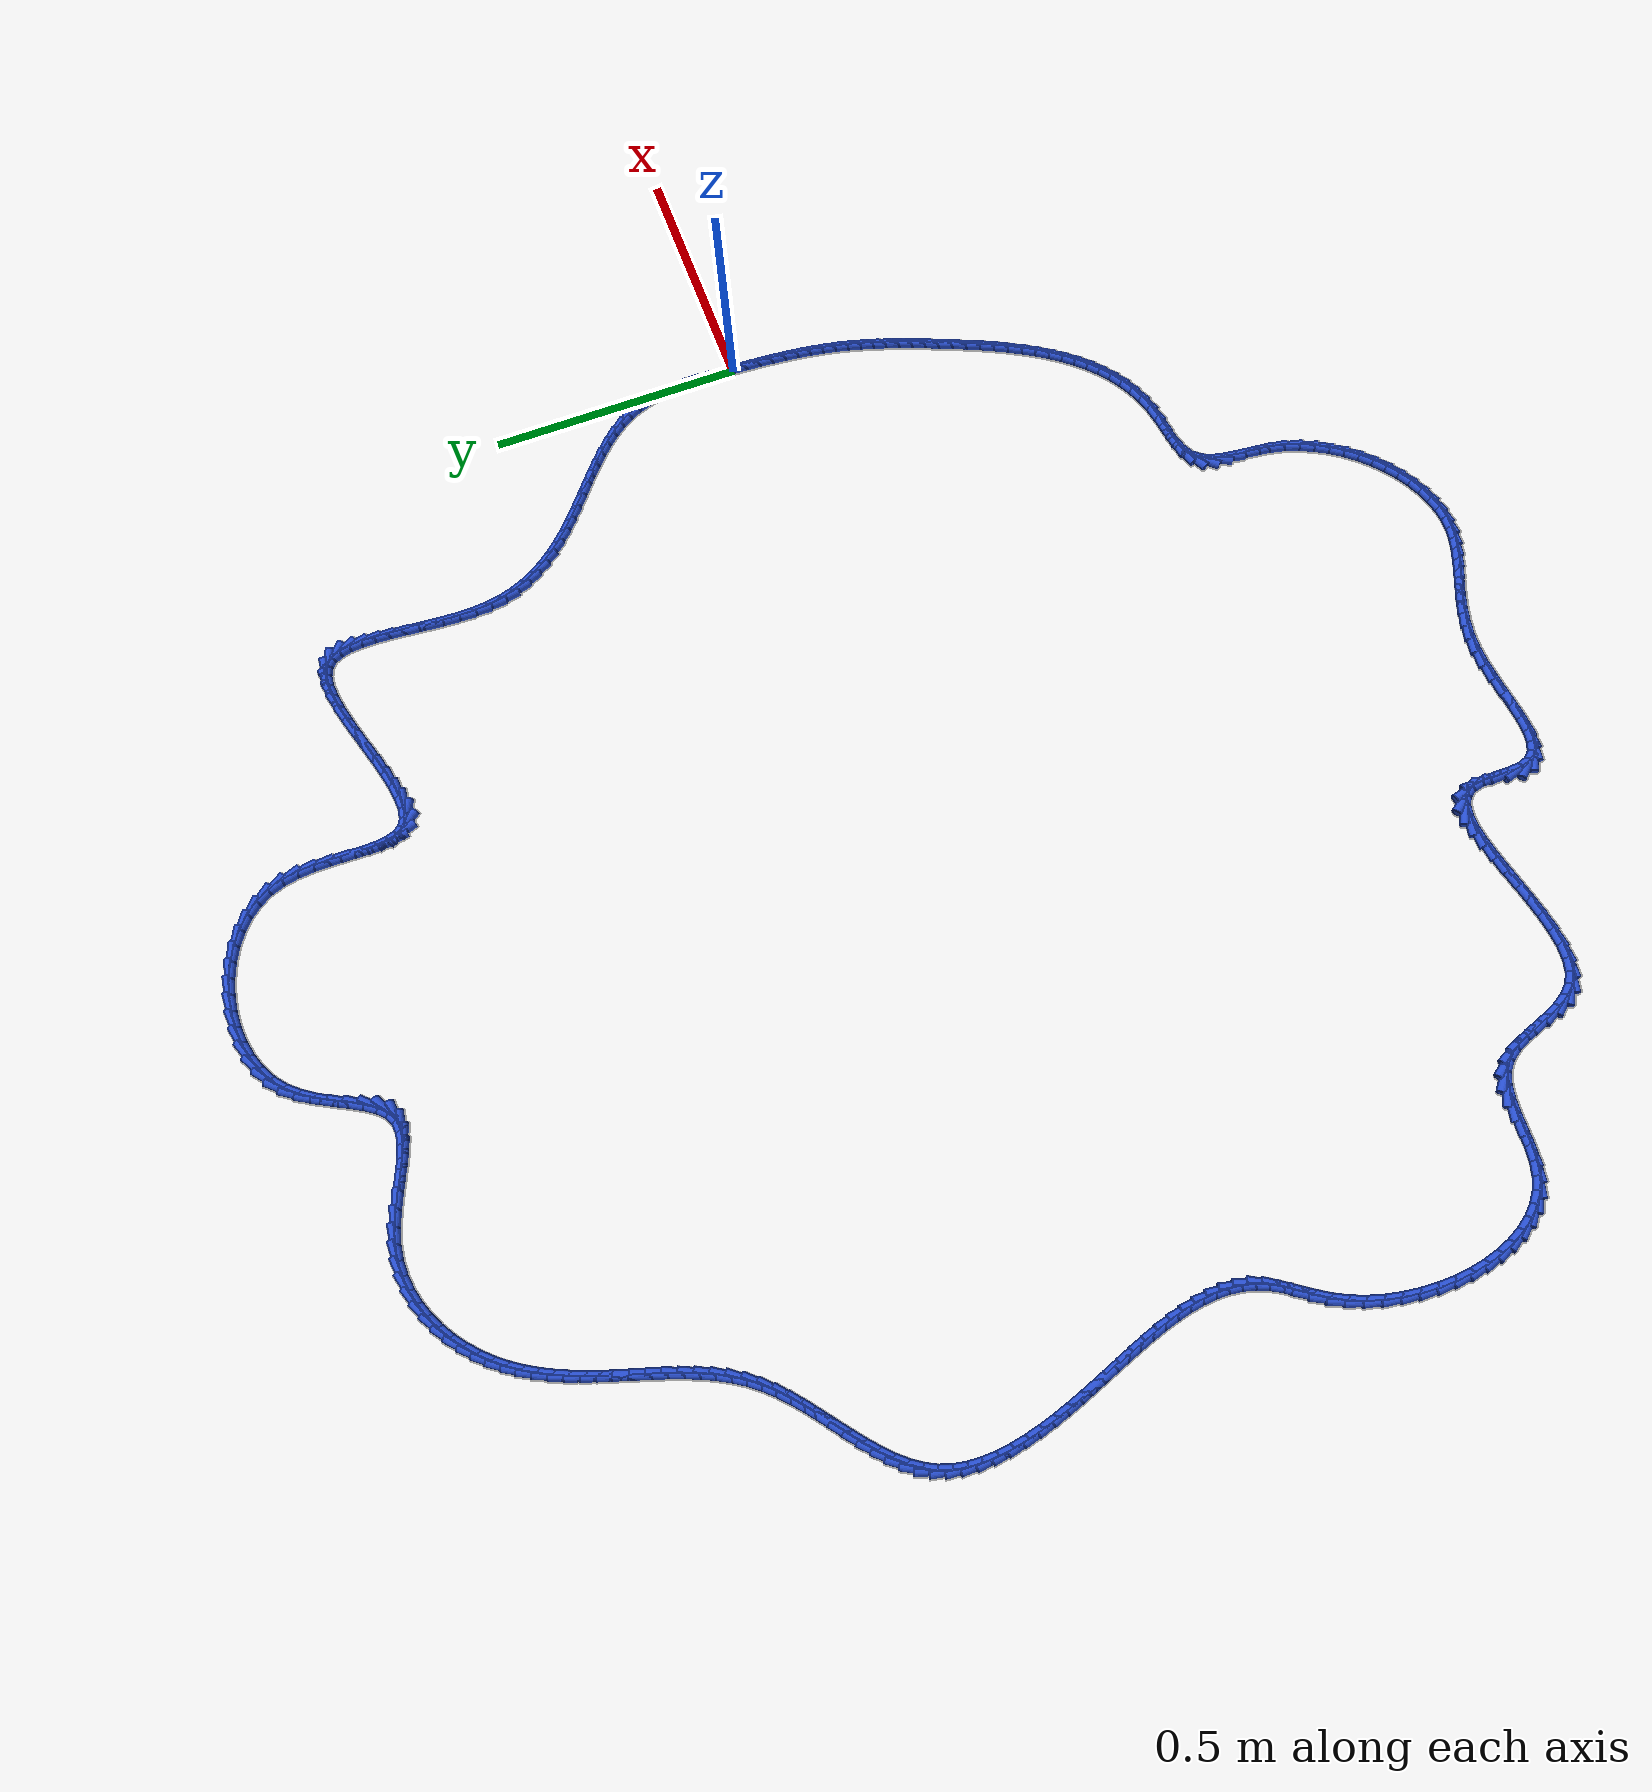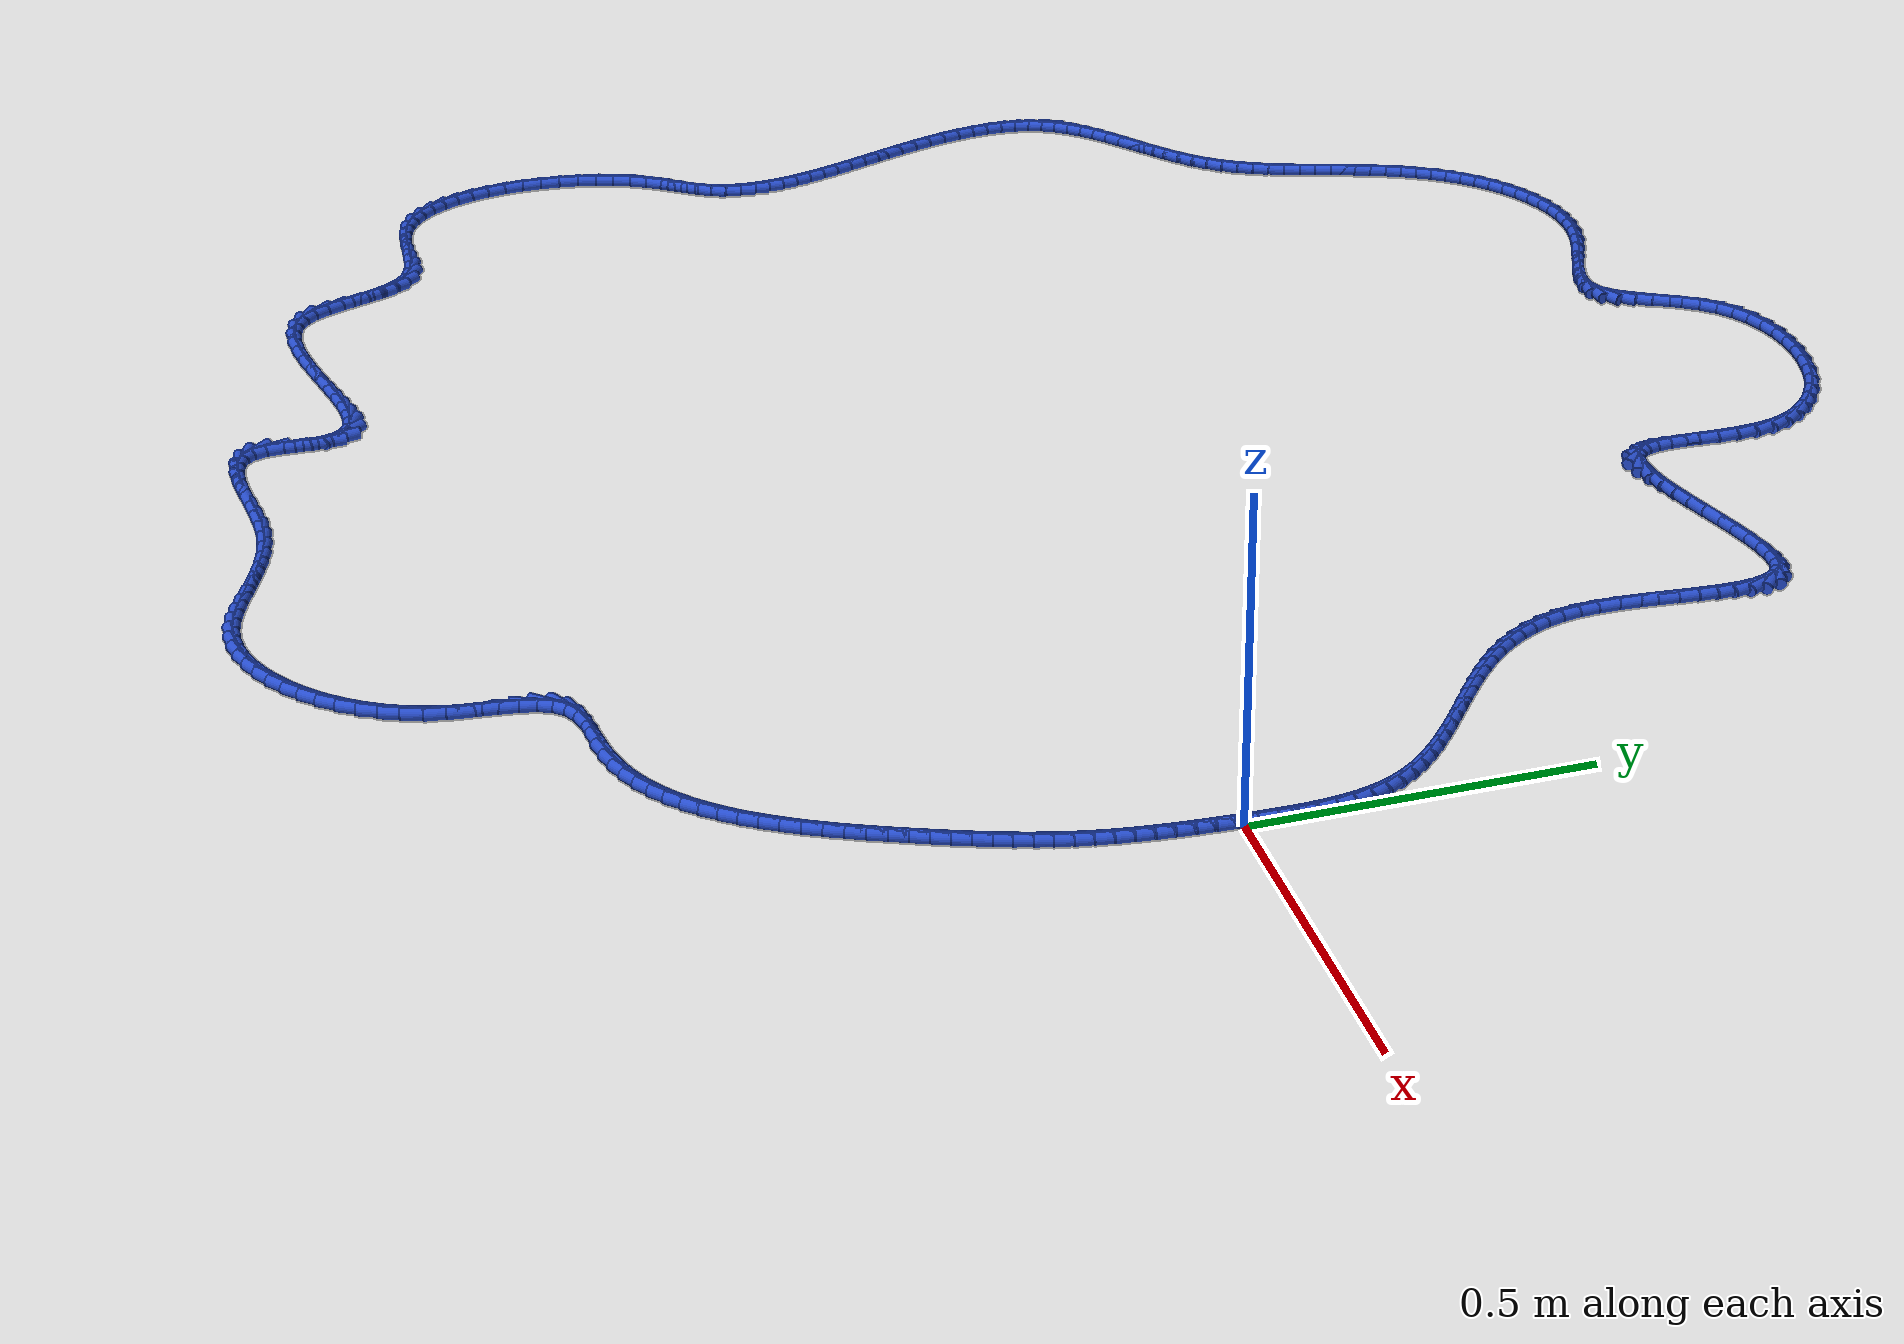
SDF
<sdf version="1.6">
 <world name="default">
  <light name="sun" type="directional">
   <pose>0 0 10 0 -0 0</pose>
   <diffuse>0.8 0.8 0.8 1</diffuse>
   <specular>0.2 0.2 0.2 1</specular>
   <attenuation>
    <range>1000</range>
    <constant>0.9</constant>
    <linear>0.01</linear>
    <quadratic>0.001</quadratic>
   </attenuation>
   <direction>-0.5 0.1 -0.9</direction>
  </light>
  <model name="ground_plane">
   <static>1</static>
   <link name="link">
    <collision name="collision">
     <geometry><plane><normal>0 0 1</normal><size>100 100</size></plane></geometry>
     <surface><friction><ode><mu>100</mu><mu2>50</mu2></ode></friction></surface>
    </collision>
    <visual name="visual">
     <cast_shadows>0</cast_shadows>
     <geometry><plane><normal>0 0 1</normal><size>100 100</size></plane></geometry>
     <material>
      <script><uri>file://media/materials/scripts/gazebo.material</uri><name>Gazebo/WhiteGlow</name></script>
     </material>
    </visual>
   </link>
  </model>
  <gravity>0 0 -9.8</gravity>
  <magnetic_field>6e-06 2.3e-05 -4.2e-05</magnetic_field>
  <atmosphere type="adiabatic"/>
  <physics name="default_physics" default="0" type="ode">
   <max_step_size>0.001</max_step_size>
   <real_time_factor>1</real_time_factor>
   <real_time_update_rate>1000</real_time_update_rate>
  </physics>
  <scene><ambient>0.4 0.4 0.4 1</ambient><background>0.7 0.7 0.7 1</background><shadows>1</shadows></scene>
  <spherical_coordinates>
   <surface_model>EARTH_WGS84</surface_model>
   <latitude_deg>0</latitude_deg>
   <longitude_deg>0</longitude_deg>
   <elevation>0</elevation>
   <heading_deg>0</heading_deg>
  </spherical_coordinates>
  <model name="line">
   <link name="link_0">
    <pose>9.324138683375338e-18 3.469446951953614e-17 0.01 0 1.57 1.5323219815487206</pose>
    <collision name="collision">
     <geometry><cylinder><radius>0.01</radius><length>0.08</length></cylinder></geometry>
    </collision>
    <visual name="visual">
     <material>
      <script><name>Gazebo/Blue</name><uri>file://media/materials/scripts/gazebo.material</uri></script>
     </material>
     <geometry><cylinder><radius>0.01</radius><length>0.08</length></cylinder></geometry>
    </visual>
   </link>
   <link name="link_1">
    <pose>0.0010711083507516086 0.02782580912069063 0.01 0 1.57 1.5497142666336148</pose>
    <collision name="collision">
     <geometry><cylinder><radius>0.01</radius><length>0.08</length></cylinder></geometry>
    </collision>
    <visual name="visual">
     <material>
      <script><name>Gazebo/Blue</name><uri>file://media/materials/scripts/gazebo.material</uri></script>
     </material>
     <geometry><cylinder><radius>0.01</radius><length>0.08</length></cylinder></geometry>
    </visual>
   </link>
   <link name="link_2">
    <pose>0.0016596048798578349 0.05573623796971701 0.01 0 1.57 -1.5633033248760873</pose>
    <collision name="collision">
     <geometry><cylinder><radius>0.01</radius><length>0.08</length></cylinder></geometry>
    </collision>
    <visual name="visual">
     <material>
      <script><name>Gazebo/Blue</name><uri>file://media/materials/scripts/gazebo.material</uri></script>
     </material>
     <geometry><cylinder><radius>0.01</radius><length>0.08</length></cylinder></geometry>
    </visual>
   </link>
   <link name="link_3">
    <pose>0.0014514285237242834 0.08351848897521835 0.01 0 1.57 -1.5227702748810366</pose>
    <collision name="collision">
     <geometry><cylinder><radius>0.01</radius><length>0.08</length></cylinder></geometry>
    </collision>
    <visual name="visual">
     <material>
      <script><name>Gazebo/Blue</name><uri>file://media/materials/scripts/gazebo.material</uri></script>
     </material>
     <geometry><cylinder><radius>0.01</radius><length>0.08</length></cylinder></geometry>
    </visual>
   </link>
   <link name="link_4">
    <pose>0.00013251821875655137 0.11095976456533392 0.01 0 1.57 -1.4691044345274904</pose>
    <collision name="collision">
     <geometry><cylinder><radius>0.01</radius><length>0.08</length></cylinder></geometry>
    </collision>
    <visual name="visual">
     <material>
      <script><name>Gazebo/Blue</name><uri>file://media/materials/scripts/gazebo.material</uri></script>
     </material>
     <geometry><cylinder><radius>0.01</radius><length>0.08</length></cylinder></geometry>
    </visual>
   </link>
   <link name="link_5">
    <pose>-0.002611187098639764 0.1378472671682029 0.01 0 1.57 -1.400843733810222</pose>
    <collision name="collision">
     <geometry><cylinder><radius>0.01</radius><length>0.08</length></cylinder></geometry>
    </collision>
    <visual name="visual">
     <material>
      <script><name>Gazebo/Blue</name><uri>file://media/materials/scripts/gazebo.material</uri></script>
     </material>
     <geometry><cylinder><radius>0.01</radius><length>0.08</length></cylinder></geometry>
    </visual>
   </link>
   <link name="link_6">
    <pose>-0.007093748492059067 0.16396819921196445 0.01 0 1.57 -1.3164777483191943</pose>
    <collision name="collision">
     <geometry><cylinder><radius>0.01</radius><length>0.08</length></cylinder></geometry>
    </collision>
    <visual name="visual">
     <material>
      <script><name>Gazebo/Blue</name><uri>file://media/materials/scripts/gazebo.material</uri></script>
     </material>
     <geometry><cylinder><radius>0.01</radius><length>0.08</length></cylinder></geometry>
    </visual>
   </link>
   <link name="link_7">
    <pose>-0.013629227025095763 0.18910976312475786 0.01 0 1.57 -1.2149048669875717</pose>
    <collision name="collision">
     <geometry><cylinder><radius>0.01</radius><length>0.08</length></cylinder></geometry>
    </collision>
    <visual name="visual">
     <material>
      <script><name>Gazebo/Blue</name><uri>file://media/materials/scripts/gazebo.material</uri></script>
     </material>
     <geometry><cylinder><radius>0.01</radius><length>0.08</length></cylinder></geometry>
    </visual>
   </link>
   <link name="link_8">
    <pose>-0.022531683761344255 0.2130591613347223 0.01 0 1.57 -1.0999398042648565</pose>
    <collision name="collision">
     <geometry><cylinder><radius>0.01</radius><length>0.08</length></cylinder></geometry>
    </collision>
    <visual name="visual">
     <material>
      <script><name>Gazebo/Blue</name><uri>file://media/materials/scripts/gazebo.material</uri></script>
     </material>
     <geometry><cylinder><radius>0.01</radius><length>0.08</length></cylinder></geometry>
    </visual>
   </link>
   <link name="link_9">
    <pose>-0.03403341591915063 0.23565393602419726 0.01 0 1.57 -0.992904981831658</pose>
    <collision name="collision">
     <geometry><cylinder><radius>0.01</radius><length>0.08</length></cylinder></geometry>
    </collision>
    <visual name="visual">
     <material>
      <script><name>Gazebo/Blue</name><uri>file://media/materials/scripts/gazebo.material</uri></script>
     </material>
     <geometry><cylinder><radius>0.01</radius><length>0.08</length></cylinder></geometry>
    </visual>
   </link>
   <link name="link_10">
    <pose>-0.04794767366931354 0.25698962513523477 0.01 0 1.57 -0.9020295866422652</pose>
    <collision name="collision">
     <geometry><cylinder><radius>0.01</radius><length>0.08</length></cylinder></geometry>
    </collision>
    <visual name="visual">
     <material>
      <script><name>Gazebo/Blue</name><uri>file://media/materials/scripts/gazebo.material</uri></script>
     </material>
     <geometry><cylinder><radius>0.01</radius><length>0.08</length></cylinder></geometry>
    </visual>
   </link>
   <link name="link_11">
    <pose>-0.06395382332059835 0.2772441952271527 0.01 0 1.57 -0.8277685829872988</pose>
    <collision name="collision">
     <geometry><cylinder><radius>0.01</radius><length>0.08</length></cylinder></geometry>
    </collision>
    <visual name="visual">
     <material>
      <script><name>Gazebo/Blue</name><uri>file://media/materials/scripts/gazebo.material</uri></script>
     </material>
     <geometry><cylinder><radius>0.01</radius><length>0.08</length></cylinder></geometry>
    </visual>
   </link>
   <link name="link_12">
    <pose>-0.08173117221646523 0.296595649162588 0.01 0 1.57 -0.7695091924597142</pose>
    <collision name="collision">
     <geometry><cylinder><radius>0.01</radius><length>0.08</length></cylinder></geometry>
    </collision>
    <visual name="visual">
     <material>
      <script><name>Gazebo/Blue</name><uri>file://media/materials/scripts/gazebo.material</uri></script>
     </material>
     <geometry><cylinder><radius>0.01</radius><length>0.08</length></cylinder></geometry>
    </visual>
   </link>
   <link name="link_13">
    <pose>-0.10095902770037428 0.31522198980417754 0.01 0 1.57 -0.726190054199158</pose>
    <collision name="collision">
     <geometry><cylinder><radius>0.01</radius><length>0.08</length></cylinder></geometry>
    </collision>
    <visual name="visual">
     <material>
      <script><name>Gazebo/Blue</name><uri>file://media/materials/scripts/gazebo.material</uri></script>
     </material>
     <geometry><cylinder><radius>0.01</radius><length>0.08</length></cylinder></geometry>
    </visual>
   </link>
   <link name="link_14">
    <pose>-0.1213166971157856 0.3333012200145582 0.01 0 1.57 -0.6967182305172623</pose>
    <collision name="collision">
     <geometry><cylinder><radius>0.01</radius><length>0.08</length></cylinder></geometry>
    </collision>
    <visual name="visual">
     <material>
      <script><name>Gazebo/Blue</name><uri>file://media/materials/scripts/gazebo.material</uri></script>
     </material>
     <geometry><cylinder><radius>0.01</radius><length>0.08</length></cylinder></geometry>
    </visual>
   </link>
   <link name="link_15">
    <pose>-0.14248348780615938 0.35101134265636696 0.01 0 1.57 -0.6802031845086991</pose>
    <collision name="collision">
     <geometry><cylinder><radius>0.01</radius><length>0.08</length></cylinder></geometry>
    </collision>
    <visual name="visual">
     <material>
      <script><name>Gazebo/Blue</name><uri>file://media/materials/scripts/gazebo.material</uri></script>
     </material>
     <geometry><cylinder><radius>0.01</radius><length>0.08</length></cylinder></geometry>
    </visual>
   </link>
   <link name="link_16">
    <pose>-0.1641387071149557 0.36853036059224076 0.01 0 1.57 -0.6760681796360968</pose>
    <collision name="collision">
     <geometry><cylinder><radius>0.01</radius><length>0.08</length></cylinder></geometry>
    </collision>
    <visual name="visual">
     <material>
      <script><name>Gazebo/Blue</name><uri>file://media/materials/scripts/gazebo.material</uri></script>
     </material>
     <geometry><cylinder><radius>0.01</radius><length>0.08</length></cylinder></geometry>
    </visual>
   </link>
   <link name="link_17">
    <pose>-0.18596166238563477 0.3860362766848165 0.01 0 1.57 -0.6840913972933165</pose>
    <collision name="collision">
     <geometry><cylinder><radius>0.01</radius><length>0.08</length></cylinder></geometry>
    </collision>
    <visual name="visual">
     <material>
      <script><name>Gazebo/Blue</name><uri>file://media/materials/scripts/gazebo.material</uri></script>
     </material>
     <geometry><cylinder><radius>0.01</radius><length>0.08</length></cylinder></geometry>
    </visual>
   </link>
   <link name="link_18">
    <pose>-0.20763166096165664 0.4037070937967312 0.01 0 1.57 -0.7044070738249729</pose>
    <collision name="collision">
     <geometry><cylinder><radius>0.01</radius><length>0.08</length></cylinder></geometry>
    </collision>
    <visual name="visual">
     <material>
      <script><name>Gazebo/Blue</name><uri>file://media/materials/scripts/gazebo.material</uri></script>
     </material>
     <geometry><cylinder><radius>0.01</radius><length>0.08</length></cylinder></geometry>
    </visual>
   </link>
   <link name="link_19">
    <pose>-0.22882801018648152 0.4217208147906216 0.01 0 1.57 -0.7374713700381726</pose>
    <collision name="collision">
     <geometry><cylinder><radius>0.01</radius><length>0.08</length></cylinder></geometry>
    </collision>
    <visual name="visual">
     <material>
      <script><name>Gazebo/Blue</name><uri>file://media/materials/scripts/gazebo.material</uri></script>
     </material>
     <geometry><cylinder><radius>0.01</radius><length>0.08</length></cylinder></geometry>
    </visual>
   </link>
   <link name="link_20">
    <pose>-0.2492301631041366 0.4402554234602079 0.01 0 1.57 -0.7832770899331617</pose>
    <collision name="collision">
     <geometry><cylinder><radius>0.01</radius><length>0.08</length></cylinder></geometry>
    </collision>
    <visual name="visual">
     <material>
      <script><name>Gazebo/Blue</name><uri>file://media/materials/scripts/gazebo.material</uri></script>
     </material>
     <geometry><cylinder><radius>0.01</radius><length>0.08</length></cylinder></geometry>
    </visual>
   </link>
   <link name="link_21">
    <pose>-0.2685421745378144 0.45948568378141497 0.01 0 1.57 -0.8409162412115178</pose>
    <collision name="collision">
     <geometry><cylinder><radius>0.01</radius><length>0.08</length></cylinder></geometry>
    </collision>
    <visual name="visual">
     <material>
      <script><name>Gazebo/Blue</name><uri>file://media/materials/scripts/gazebo.material</uri></script>
     </material>
     <geometry><cylinder><radius>0.01</radius><length>0.08</length></cylinder></geometry>
    </visual>
   </link>
   <link name="link_22">
    <pose>-0.2865201827230955 0.47957954318665835 0.01 0 1.57 -0.9104443464703046</pose>
    <collision name="collision">
     <geometry><cylinder><radius>0.01</radius><length>0.08</length></cylinder></geometry>
    </collision>
    <visual name="visual">
     <material>
      <script><name>Gazebo/Blue</name><uri>file://media/materials/scripts/gazebo.material</uri></script>
     </material>
     <geometry><cylinder><radius>0.01</radius><length>0.08</length></cylinder></geometry>
    </visual>
   </link>
   <link name="link_23">
    <pose>-0.3029269577387636 0.5007040811497155 0.01 0 1.57 -0.9916290297961323</pose>
    <collision name="collision">
     <geometry><cylinder><radius>0.01</radius><length>0.08</length></cylinder></geometry>
    </collision>
    <visual name="visual">
     <material>
      <script><name>Gazebo/Blue</name><uri>file://media/materials/scripts/gazebo.material</uri></script>
     </material>
     <geometry><cylinder><radius>0.01</radius><length>0.08</length></cylinder></geometry>
    </visual>
   </link>
   <link name="link_24">
    <pose>-0.317525269663603 0.5230263771443634 0.01 0 1.57 -1.0834892252430475</pose>
    <collision name="collision">
     <geometry><cylinder><radius>0.01</radius><length>0.08</length></cylinder></geometry>
    </collision>
    <visual name="visual">
     <material>
      <script><name>Gazebo/Blue</name><uri>file://media/materials/scripts/gazebo.material</uri></script>
     </material>
     <geometry><cylinder><radius>0.01</radius><length>0.08</length></cylinder></geometry>
    </visual>
   </link>
   <link name="link_25">
    <pose>-0.3300778885763975 0.546713510644379 0.01 0 1.57 -1.1840815447950934</pose>
    <collision name="collision">
     <geometry><cylinder><radius>0.01</radius><length>0.08</length></cylinder></geometry>
    </collision>
    <visual name="visual">
     <material>
      <script><name>Gazebo/Blue</name><uri>file://media/materials/scripts/gazebo.material</uri></script>
     </material>
     <geometry><cylinder><radius>0.01</radius><length>0.08</length></cylinder></geometry>
    </visual>
   </link>
   <link name="link_26">
    <pose>-0.3403475845559311 0.5719325611235392 0.01 0 1.57 -1.2904826595977297</pose>
    <collision name="collision">
     <geometry><cylinder><radius>0.01</radius><length>0.08</length></cylinder></geometry>
    </collision>
    <visual name="visual">
     <material>
      <script><name>Gazebo/Blue</name><uri>file://media/materials/scripts/gazebo.material</uri></script>
     </material>
     <geometry><cylinder><radius>0.01</radius><length>0.08</length></cylinder></geometry>
    </visual>
   </link>
   <link name="link_27">
    <pose>-0.3480971276809878 0.5988506080556208 0.01 0 1.57 -1.3990666883644753</pose>
    <collision name="collision">
     <geometry><cylinder><radius>0.01</radius><length>0.08</length></cylinder></geometry>
    </collision>
    <visual name="visual">
     <material>
      <script><name>Gazebo/Blue</name><uri>file://media/materials/scripts/gazebo.material</uri></script>
     </material>
     <geometry><cylinder><radius>0.01</radius><length>0.08</length></cylinder></geometry>
    </visual>
   </link>
   <link name="link_28">
    <pose>-0.3530893740554741 0.6276346554776399 0.01 0 1.57 -1.4995953994509539</pose>
    <collision name="collision">
     <geometry><cylinder><radius>0.01</radius><length>0.08</length></cylinder></geometry>
    </collision>
    <visual name="visual">
     <material>
      <script><name>Gazebo/Blue</name><uri>file://media/materials/scripts/gazebo.material</uri></script>
     </material>
     <geometry><cylinder><radius>0.01</radius><length>0.08</length></cylinder></geometry>
    </visual>
   </link>
   <link name="link_29">
    <pose>-0.35527551323244955 0.6582865549102765 0.01 0 1.57 1.568259517518006</pose>
    <collision name="collision">
     <geometry><cylinder><radius>0.01</radius><length>0.08</length></cylinder></geometry>
    </collision>
    <visual name="visual">
     <material>
      <script><name>Gazebo/Blue</name><uri>file://media/materials/scripts/gazebo.material</uri></script>
     </material>
     <geometry><cylinder><radius>0.01</radius><length>0.08</length></cylinder></geometry>
    </visual>
   </link>
   <link name="link_30">
    <pose>-0.3551943190750306 0.6902928960988796 0.01 0 1.57 1.5190675632285404</pose>
    <collision name="collision">
     <geometry><cylinder><radius>0.01</radius><length>0.08</length></cylinder></geometry>
    </collision>
    <visual name="visual">
     <material>
      <script><name>Gazebo/Blue</name><uri>file://media/materials/scripts/gazebo.material</uri></script>
     </material>
     <geometry><cylinder><radius>0.01</radius><length>0.08</length></cylinder></geometry>
    </visual>
   </link>
   <link name="link_31">
    <pose>-0.35349883604991483 0.7230400631279896 0.01 0 1.57 1.490157040372215</pose>
    <collision name="collision">
     <geometry><cylinder><radius>0.01</radius><length>0.08</length></cylinder></geometry>
    </collision>
    <visual name="visual">
     <material>
      <script><name>Gazebo/Blue</name><uri>file://media/materials/scripts/gazebo.material</uri></script>
     </material>
     <geometry><cylinder><radius>0.01</radius><length>0.08</length></cylinder></geometry>
    </visual>
   </link>
   <link name="link_32">
    <pose>-0.3508421086238002 0.7559144400821477 0.01 0 1.57 1.4795066805859032</pose>
    <collision name="collision">
     <geometry><cylinder><radius>0.01</radius><length>0.08</length></cylinder></geometry>
    </collision>
    <visual name="visual">
     <material>
      <script><name>Gazebo/Blue</name><uri>file://media/materials/scripts/gazebo.material</uri></script>
     </material>
     <geometry><cylinder><radius>0.01</radius><length>0.08</length></cylinder></geometry>
    </visual>
   </link>
   <link name="link_33">
    <pose>-0.3478771812633844 0.7883024110458939 0.01 0 1.57 1.4872502951203692</pose>
    <collision name="collision">
     <geometry><cylinder><radius>0.01</radius><length>0.08</length></cylinder></geometry>
    </collision>
    <visual name="visual">
     <material>
      <script><name>Gazebo/Blue</name><uri>file://media/materials/scripts/gazebo.material</uri></script>
     </material>
     <geometry><cylinder><radius>0.01</radius><length>0.08</length></cylinder></geometry>
    </visual>
   </link>
   <link name="link_34">
    <pose>-0.3452570984353651 0.8195903601037692 0.01 0 1.57 1.5159997887330037</pose>
    <collision name="collision">
     <geometry><cylinder><radius>0.01</radius><length>0.08</length></cylinder></geometry>
    </collision>
    <visual name="visual">
     <material>
      <script><name>Gazebo/Blue</name><uri>file://media/materials/scripts/gazebo.material</uri></script>
     </material>
     <geometry><cylinder><radius>0.01</radius><length>0.08</length></cylinder></geometry>
    </visual>
   </link>
   <link name="link_35">
    <pose>-0.34363490460644036 0.8491646713403145 0.01 0 1.57 -1.569741547716111</pose>
    <collision name="collision">
     <geometry><cylinder><radius>0.01</radius><length>0.08</length></cylinder></geometry>
    </collision>
    <visual name="visual">
     <material>
      <script><name>Gazebo/Blue</name><uri>file://media/materials/scripts/gazebo.material</uri></script>
     </material>
     <geometry><cylinder><radius>0.01</radius><length>0.08</length></cylinder></geometry>
    </visual>
   </link>
   <link name="link_36">
    <pose>-0.34366364424330775 0.8764117288400705 0.01 0 1.57 -1.4751171955712417</pose>
    <collision name="collision">
     <geometry><cylinder><radius>0.01</radius><length>0.08</length></cylinder></geometry>
    </collision>
    <visual name="visual">
     <material>
      <script><name>Gazebo/Blue</name><uri>file://media/materials/scripts/gazebo.material</uri></script>
     </material>
     <geometry><cylinder><radius>0.01</radius><length>0.08</length></cylinder></geometry>
    </visual>
   </link>
   <link name="link_37">
    <pose>-0.34599636181266513 0.9007179166875775 0.01 0 1.57 -1.3212053123291074</pose>
    <collision name="collision">
     <geometry><cylinder><radius>0.01</radius><length>0.08</length></cylinder></geometry>
    </collision>
    <visual name="visual">
     <material>
      <script><name>Gazebo/Blue</name><uri>file://media/materials/scripts/gazebo.material</uri></script>
     </material>
     <geometry><cylinder><radius>0.01</radius><length>0.08</length></cylinder></geometry>
    </visual>
   </link>
   <link name="link_38">
    <pose>-0.3512861017812102 0.9214696189673763 0.01 0 1.57 -1.078250196329859</pose>
    <collision name="collision">
     <geometry><cylinder><radius>0.01</radius><length>0.08</length></cylinder></geometry>
    </collision>
    <visual name="visual">
     <material>
      <script><name>Gazebo/Blue</name><uri>file://media/materials/scripts/gazebo.material</uri></script>
     </material>
     <geometry><cylinder><radius>0.01</radius><length>0.08</length></cylinder></geometry>
    </visual>
   </link>
   <link name="link_39">
    <pose>-0.3601859086156409 0.9380532197640081 0.01 0 1.57 -0.7309339318425149</pose>
    <collision name="collision">
     <geometry><cylinder><radius>0.01</radius><length>0.08</length></cylinder></geometry>
    </collision>
    <visual name="visual">
     <material>
      <script><name>Gazebo/Blue</name><uri>file://media/materials/scripts/gazebo.material</uri></script>
     </material>
     <geometry><cylinder><radius>0.01</radius><length>0.08</length></cylinder></geometry>
    </visual>
   </link>
   <link name="link_40">
    <pose>-0.3733488267826549 0.9498551031620132 0.01 0 1.57 -0.35127036046358423</pose>
    <collision name="collision">
     <geometry><cylinder><radius>0.01</radius><length>0.08</length></cylinder></geometry>
    </collision>
    <visual name="visual">
     <material>
      <script><name>Gazebo/Blue</name><uri>file://media/materials/scripts/gazebo.material</uri></script>
     </material>
     <geometry><cylinder><radius>0.01</radius><length>0.08</length></cylinder></geometry>
    </visual>
   </link>
   <link name="link_41">
    <pose>-0.39126987315338213 0.9564226074155797 0.01 0 1.57 -0.08125241056327141</pose>
    <collision name="collision">
     <geometry><cylinder><radius>0.01</radius><length>0.08</length></cylinder></geometry>
    </collision>
    <visual name="visual">
     <material>
      <script><name>Gazebo/Blue</name><uri>file://media/materials/scripts/gazebo.material</uri></script>
     </material>
     <geometry><cylinder><radius>0.01</radius><length>0.08</length></cylinder></geometry>
    </visual>
   </link>
   <link name="link_42">
    <pose>-0.41352888729481413 0.958235196605014 0.01 0 1.57 0.08214575033104163</pose>
    <collision name="collision">
     <geometry><cylinder><radius>0.01</radius><length>0.08</length></cylinder></geometry>
    </collision>
    <visual name="visual">
     <material>
      <script><name>Gazebo/Blue</name><uri>file://media/materials/scripts/gazebo.material</uri></script>
     </material>
     <geometry><cylinder><radius>0.01</radius><length>0.08</length></cylinder></geometry>
    </visual>
   </link>
   <link name="link_43">
    <pose>-0.4393770384408317 0.9561070919165768 0.01 0 1.57 0.18114001203333813</pose>
    <collision name="collision">
     <geometry><cylinder><radius>0.01</radius><length>0.08</length></cylinder></geometry>
    </collision>
    <visual name="visual">
     <material>
      <script><name>Gazebo/Blue</name><uri>file://media/materials/scripts/gazebo.material</uri></script>
     </material>
     <geometry><cylinder><radius>0.01</radius><length>0.08</length></cylinder></geometry>
    </visual>
   </link>
   <link name="link_44">
    <pose>-0.46806506832106787 0.9508529499578967 0.01 0 1.57 0.24102582659216687</pose>
    <collision name="collision">
     <geometry><cylinder><radius>0.01</radius><length>0.08</length></cylinder></geometry>
    </collision>
    <visual name="visual">
     <material>
      <script><name>Gazebo/Blue</name><uri>file://media/materials/scripts/gazebo.material</uri></script>
     </material>
     <geometry><cylinder><radius>0.01</radius><length>0.08</length></cylinder></geometry>
    </visual>
   </link>
   <link name="link_45">
    <pose>-0.49884371866515403 0.9432874273366004 0.01 0 1.57 0.274989318874367</pose>
    <collision name="collision">
     <geometry><cylinder><radius>0.01</radius><length>0.08</length></cylinder></geometry>
    </collision>
    <visual name="visual">
     <material>
      <script><name>Gazebo/Blue</name><uri>file://media/materials/scripts/gazebo.material</uri></script>
     </material>
     <geometry><cylinder><radius>0.01</radius><length>0.08</length></cylinder></geometry>
    </visual>
   </link>
   <link name="link_46">
    <pose>-0.5309637312027223 0.9342251806603161 0.01 0 1.57 0.28951151797443164</pose>
    <collision name="collision">
     <geometry><cylinder><radius>0.01</radius><length>0.08</length></cylinder></geometry>
    </collision>
    <visual name="visual">
     <material>
      <script><name>Gazebo/Blue</name><uri>file://media/materials/scripts/gazebo.material</uri></script>
     </material>
     <geometry><cylinder><radius>0.01</radius><length>0.08</length></cylinder></geometry>
    </visual>
   </link>
   <link name="link_47">
    <pose>-0.5636758476634055 0.9244808665366708 0.01 0 1.57 0.28708971415917006</pose>
    <collision name="collision">
     <geometry><cylinder><radius>0.01</radius><length>0.08</length></cylinder></geometry>
    </collision>
    <visual name="visual">
     <material>
      <script><name>Gazebo/Blue</name><uri>file://media/materials/scripts/gazebo.material</uri></script>
     </material>
     <geometry><cylinder><radius>0.01</radius><length>0.08</length></cylinder></geometry>
    </visual>
   </link>
   <link name="link_48">
    <pose>-0.5962308097768352 0.9148691415732924 0.01 0 1.57 0.26722397066394293</pose>
    <collision name="collision">
     <geometry><cylinder><radius>0.01</radius><length>0.08</length></cylinder></geometry>
    </collision>
    <visual name="visual">
     <material>
      <script><name>Gazebo/Blue</name><uri>file://media/materials/scripts/gazebo.material</uri></script>
     </material>
     <geometry><cylinder><radius>0.01</radius><length>0.08</length></cylinder></geometry>
    </visual>
   </link>
   <link name="link_49">
    <pose>-0.6278793592726438 0.906204662377808 0.01 0 1.57 0.22620184832455223</pose>
    <collision name="collision">
     <geometry><cylinder><radius>0.01</radius><length>0.08</length></cylinder></geometry>
    </collision>
    <visual name="visual">
     <material>
      <script><name>Gazebo/Blue</name><uri>file://media/materials/scripts/gazebo.material</uri></script>
     </material>
     <geometry><cylinder><radius>0.01</radius><length>0.08</length></cylinder></geometry>
    </visual>
   </link>
   <link name="link_50">
    <pose>-0.657872237880463 0.8993020855578453 0.01 0 1.57 0.15554163273530774</pose>
    <collision name="collision">
     <geometry><cylinder><radius>0.01</radius><length>0.08</length></cylinder></geometry>
    </collision>
    <visual name="visual">
     <material>
      <script><name>Gazebo/Blue</name><uri>file://media/materials/scripts/gazebo.material</uri></script>
     </material>
     <geometry><cylinder><radius>0.01</radius><length>0.08</length></cylinder></geometry>
    </visual>
   </link>
   <link name="link_51">
    <pose>-0.6854601873299251 0.8949760677210318 0.01 0 1.57 0.03823997910304859</pose>
    <collision name="collision">
     <geometry><cylinder><radius>0.01</radius><length>0.08</length></cylinder></geometry>
    </collision>
    <visual name="visual">
     <material>
      <script><name>Gazebo/Blue</name><uri>file://media/materials/scripts/gazebo.material</uri></script>
     </material>
     <geometry><cylinder><radius>0.01</radius><length>0.08</length></cylinder></geometry>
    </visual>
   </link>
   <link name="link_52">
    <pose>-0.7098939493506625 0.8940412654749949 0.01 0 1.57 -0.15800071380295008</pose>
    <collision name="collision">
     <geometry><cylinder><radius>0.01</radius><length>0.08</length></cylinder></geometry>
    </collision>
    <visual name="visual">
     <material>
      <script><name>Gazebo/Blue</name><uri>file://media/materials/scripts/gazebo.material</uri></script>
     </material>
     <geometry><cylinder><radius>0.01</radius><length>0.08</length></cylinder></geometry>
    </visual>
   </link>
   <link name="link_53">
    <pose>-0.7304242656723073 0.897312335427362 0.01 0 1.57 -0.481264790733699</pose>
    <collision name="collision">
     <geometry><cylinder><radius>0.01</radius><length>0.08</length></cylinder></geometry>
    </collision>
    <visual name="visual">
     <material>
      <script><name>Gazebo/Blue</name><uri>file://media/materials/scripts/gazebo.material</uri></script>
     </material>
     <geometry><cylinder><radius>0.01</radius><length>0.08</length></cylinder></geometry>
    </visual>
   </link>
   <link name="link_54">
    <pose>-0.7463018780244912 0.9056039341857609 0.01 0 1.57 -0.9185276640830071</pose>
    <collision name="collision">
     <geometry><cylinder><radius>0.01</radius><length>0.08</length></cylinder></geometry>
    </collision>
    <visual name="visual">
     <material>
      <script><name>Gazebo/Blue</name><uri>file://media/materials/scripts/gazebo.material</uri></script>
     </material>
     <geometry><cylinder><radius>0.01</radius><length>0.08</length></cylinder></geometry>
    </visual>
   </link>
   <link name="link_55">
    <pose>-0.7569620947352252 0.9195609276097089 0.01 0 1.57 -1.2630967971118676</pose>
    <collision name="collision">
     <geometry><cylinder><radius>0.01</radius><length>0.08</length></cylinder></geometry>
    </collision>
    <visual name="visual">
     <material>
      <script><name>Gazebo/Blue</name><uri>file://media/materials/scripts/gazebo.material</uri></script>
     </material>
     <geometry><cylinder><radius>0.01</radius><length>0.08</length></cylinder></geometry>
    </visual>
   </link>
   <link name="link_56">
    <pose>-0.7630493837037606 0.9387158236890526 0.01 0 1.57 -1.4583936111009894</pose>
    <collision name="collision">
     <geometry><cylinder><radius>0.01</radius><length>0.08</length></cylinder></geometry>
    </collision>
    <visual name="visual">
     <material>
      <script><name>Gazebo/Blue</name><uri>file://media/materials/scripts/gazebo.material</uri></script>
     </material>
     <geometry><cylinder><radius>0.01</radius><length>0.08</length></cylinder></geometry>
    </visual>
   </link>
   <link name="link_57">
    <pose>-0.7656949750317199 0.9621533369384467 0.01 0 1.57 -1.5582443029590516</pose>
    <collision name="collision">
     <geometry><cylinder><radius>0.01</radius><length>0.08</length></cylinder></geometry>
    </collision>
    <visual name="visual">
     <material>
      <script><name>Gazebo/Blue</name><uri>file://media/materials/scripts/gazebo.material</uri></script>
     </material>
     <geometry><cylinder><radius>0.01</radius><length>0.08</length></cylinder></geometry>
    </visual>
   </link>
   <link name="link_58">
    <pose>-0.7660314323558962 0.9889569550962151 0.01 0 1.57 1.5420855572879484</pose>
    <collision name="collision">
     <geometry><cylinder><radius>0.01</radius><length>0.08</length></cylinder></geometry>
    </collision>
    <visual name="visual">
     <material>
      <script><name>Gazebo/Blue</name><uri>file://media/materials/scripts/gazebo.material</uri></script>
     </material>
     <geometry><cylinder><radius>0.01</radius><length>0.08</length></cylinder></geometry>
    </visual>
   </link>
   <link name="link_59">
    <pose>-0.7651913193130839 1.0182101659006806 0.01 0 1.57 1.5420862481166222</pose>
    <collision name="collision">
     <geometry><cylinder><radius>0.01</radius><length>0.08</length></cylinder></geometry>
    </collision>
    <visual name="visual">
     <material>
      <script><name>Gazebo/Blue</name><uri>file://media/materials/scripts/gazebo.material</uri></script>
     </material>
     <geometry><cylinder><radius>0.01</radius><length>0.08</length></cylinder></geometry>
    </visual>
   </link>
   <link name="link_60">
    <pose>-0.7643071995400774 1.048996457090168 0.01 0 1.57 -1.5642862748445243</pose>
    <collision name="collision">
     <geometry><cylinder><radius>0.01</radius><length>0.08</length></cylinder></geometry>
    </collision>
    <visual name="visual">
     <material>
      <script><name>Gazebo/Blue</name><uri>file://media/materials/scripts/gazebo.material</uri></script>
     </material>
     <geometry><cylinder><radius>0.01</radius><length>0.08</length></cylinder></geometry>
    </visual>
   </link>
   <link name="link_61">
    <pose>-0.7645116366736705 1.0803993164030006 0.01 0 1.57 -1.4929689462433988</pose>
    <collision name="collision">
     <geometry><cylinder><radius>0.01</radius><length>0.08</length></cylinder></geometry>
    </collision>
    <visual name="visual">
     <material>
      <script><name>Gazebo/Blue</name><uri>file://media/materials/scripts/gazebo.material</uri></script>
     </material>
     <geometry><cylinder><radius>0.01</radius><length>0.08</length></cylinder></geometry>
    </visual>
   </link>
   <link name="link_62">
    <pose>-0.7669371943506571 1.1115022315775016 0.01 0 1.57 -1.3797806796780474</pose>
    <collision name="collision">
     <geometry><cylinder><radius>0.01</radius><length>0.08</length></cylinder></geometry>
    </collision>
    <visual name="visual">
     <material>
      <script><name>Gazebo/Blue</name><uri>file://media/materials/scripts/gazebo.material</uri></script>
     </material>
     <geometry><cylinder><radius>0.01</radius><length>0.08</length></cylinder></geometry>
    </visual>
   </link>
   <link name="link_63">
    <pose>-0.7727164362078316 1.141388690351995 0.01 0 1.57 -1.2176725990502888</pose>
    <collision name="collision">
     <geometry><cylinder><radius>0.01</radius><length>0.08</length></cylinder></geometry>
    </collision>
    <visual name="visual">
     <material>
      <script><name>Gazebo/Blue</name><uri>file://media/materials/scripts/gazebo.material</uri></script>
     </material>
     <geometry><cylinder><radius>0.01</radius><length>0.08</length></cylinder></geometry>
    </visual>
   </link>
   <link name="link_64">
    <pose>-0.7829509936327925 1.169156788784172 0.01 0 1.57 -1.032894420834657</pose>
    <collision name="collision">
     <geometry><cylinder><radius>0.01</radius><length>0.08</length></cylinder></geometry>
    </collision>
    <visual name="visual">
     <material>
      <script><name>Gazebo/Blue</name><uri>file://media/materials/scripts/gazebo.material</uri></script>
     </material>
     <geometry><cylinder><radius>0.01</radius><length>0.08</length></cylinder></geometry>
    </visual>
   </link>
   <link name="link_65">
    <pose>-0.7979409267393834 1.1942831795988647 0.01 0 1.57 -0.861651325916574</pose>
    <collision name="collision">
     <geometry><cylinder><radius>0.01</radius><length>0.08</length></cylinder></geometry>
    </collision>
    <visual name="visual">
     <material>
      <script><name>Gazebo/Blue</name><uri>file://media/materials/scripts/gazebo.material</uri></script>
     </material>
     <geometry><cylinder><radius>0.01</radius><length>0.08</length></cylinder></geometry>
    </visual>
   </link>
   <link name="link_66">
    <pose>-0.8171312048167478 1.2166483477730086 0.01 0 1.57 -0.7077767998189369</pose>
    <collision name="collision">
     <geometry><cylinder><radius>0.01</radius><length>0.08</length></cylinder></geometry>
    </collision>
    <visual name="visual">
     <material>
      <script><name>Gazebo/Blue</name><uri>file://media/materials/scripts/gazebo.material</uri></script>
     </material>
     <geometry><cylinder><radius>0.01</radius><length>0.08</length></cylinder></geometry>
    </visual>
   </link>
   <link name="link_67">
    <pose>-0.8399251469751283 1.2361524483408717 0.01 0 1.57 -0.5701539982143686</pose>
    <collision name="collision">
     <geometry><cylinder><radius>0.01</radius><length>0.08</length></cylinder></geometry>
    </collision>
    <visual name="visual">
     <material>
      <script><name>Gazebo/Blue</name><uri>file://media/materials/scripts/gazebo.material</uri></script>
     </material>
     <geometry><cylinder><radius>0.01</radius><length>0.08</length></cylinder></geometry>
    </visual>
   </link>
   <link name="link_68">
    <pose>-0.8657260723247691 1.252695636336722 0.01 0 1.57 -0.44582003260957576</pose>
    <collision name="collision">
     <geometry><cylinder><radius>0.01</radius><length>0.08</length></cylinder></geometry>
    </collision>
    <visual name="visual">
     <material>
      <script><name>Gazebo/Blue</name><uri>file://media/materials/scripts/gazebo.material</uri></script>
     </material>
     <geometry><cylinder><radius>0.01</radius><length>0.08</length></cylinder></geometry>
    </visual>
   </link>
   <link name="link_69">
    <pose>-0.8939372999759121 1.2661780667948268 0.01 0 1.57 -0.3311194910486212</pose>
    <collision name="collision">
     <geometry><cylinder><radius>0.01</radius><length>0.08</length></cylinder></geometry>
    </collision>
    <visual name="visual">
     <material>
      <script><name>Gazebo/Blue</name><uri>file://media/materials/scripts/gazebo.material</uri></script>
     </material>
     <geometry><cylinder><radius>0.01</radius><length>0.08</length></cylinder></geometry>
    </visual>
   </link>
   <link name="link_70">
    <pose>-0.923962149038801 1.276499894749454 0.01 0 1.57 -0.22228846714532277</pose>
    <collision name="collision">
     <geometry><cylinder><radius>0.01</radius><length>0.08</length></cylinder></geometry>
    </collision>
    <visual name="visual">
     <material>
      <script><name>Gazebo/Blue</name><uri>file://media/materials/scripts/gazebo.material</uri></script>
     </material>
     <geometry><cylinder><radius>0.01</radius><length>0.08</length></cylinder></geometry>
    </visual>
   </link>
   <link name="link_71">
    <pose>-0.955203938623679 1.283561275234871 0.01 0 1.57 -0.11564149985590917</pose>
    <collision name="collision">
     <geometry><cylinder><radius>0.01</radius><length>0.08</length></cylinder></geometry>
    </collision>
    <visual name="visual">
     <material>
      <script><name>Gazebo/Blue</name><uri>file://media/materials/scripts/gazebo.material</uri></script>
     </material>
     <geometry><cylinder><radius>0.01</radius><length>0.08</length></cylinder></geometry>
    </visual>
   </link>
   <link name="link_72">
    <pose>-0.9870659878407896 1.2872623632853468 0.01 0 1.57 -0.007556572630497869</pose>
    <collision name="collision">
     <geometry><cylinder><radius>0.01</radius><length>0.08</length></cylinder></geometry>
    </collision>
    <visual name="visual">
     <material>
      <script><name>Gazebo/Blue</name><uri>file://media/materials/scripts/gazebo.material</uri></script>
     </material>
     <geometry><cylinder><radius>0.01</radius><length>0.08</length></cylinder></geometry>
    </visual>
   </link>
   <link name="link_73">
    <pose>-1.0189516158003753 1.2875033139351477 0.01 0 1.57 0.10560261740623014</pose>
    <collision name="collision">
     <geometry><cylinder><radius>0.01</radius><length>0.08</length></cylinder></geometry>
    </collision>
    <visual name="visual">
     <material>
      <script><name>Gazebo/Blue</name><uri>file://media/materials/scripts/gazebo.material</uri></script>
     </material>
     <geometry><cylinder><radius>0.01</radius><length>0.08</length></cylinder></geometry>
    </visual>
   </link>
   <link name="link_74">
    <pose>-1.0502641416126792 1.2841842822185414 0.01 0 1.57 0.22751819118289002</pose>
    <collision name="collision">
     <geometry><cylinder><radius>0.01</radius><length>0.08</length></cylinder></geometry>
    </collision>
    <visual name="visual">
     <material>
      <script><name>Gazebo/Blue</name><uri>file://media/materials/scripts/gazebo.material</uri></script>
     </material>
     <geometry><cylinder><radius>0.01</radius><length>0.08</length></cylinder></geometry>
    </visual>
   </link>
   <link name="link_75">
    <pose>-1.0804068843879446 1.277205423169796 0.01 0 1.57 0.36177736097876495</pose>
    <collision name="collision">
     <geometry><cylinder><radius>0.01</radius><length>0.08</length></cylinder></geometry>
    </collision>
    <visual name="visual">
     <material>
      <script><name>Gazebo/Blue</name><uri>file://media/materials/scripts/gazebo.material</uri></script>
     </material>
     <geometry><cylinder><radius>0.01</radius><length>0.08</length></cylinder></geometry>
    </visual>
   </link>
   <link name="link_76">
    <pose>-1.1087831632364145 1.26646689182318 0.01 0 1.57 0.5113861078961459</pose>
    <collision name="collision">
     <geometry><cylinder><radius>0.01</radius><length>0.08</length></cylinder></geometry>
    </collision>
    <visual name="visual">
     <material>
      <script><name>Gazebo/Blue</name><uri>file://media/materials/scripts/gazebo.material</uri></script>
     </material>
     <geometry><cylinder><radius>0.01</radius><length>0.08</length></cylinder></geometry>
    </visual>
   </link>
   <link name="link_77">
    <pose>-1.1347962972683323 1.2518688432129599 0.01 0 1.57 0.6777690725338601</pose>
    <collision name="collision">
     <geometry><cylinder><radius>0.01</radius><length>0.08</length></cylinder></geometry>
    </collision>
    <visual name="visual">
     <material>
      <script><name>Gazebo/Blue</name><uri>file://media/materials/scripts/gazebo.material</uri></script>
     </material>
     <geometry><cylinder><radius>0.01</radius><length>0.08</length></cylinder></geometry>
    </visual>
   </link>
   <link name="link_78">
    <pose>-1.1578496055939413 1.233311432373404 0.01 0 1.57 0.8499789660706343</pose>
    <collision name="collision">
     <geometry><cylinder><radius>0.01</radius><length>0.08</length></cylinder></geometry>
    </collision>
    <visual name="visual">
     <material>
      <script><name>Gazebo/Blue</name><uri>file://media/materials/scripts/gazebo.material</uri></script>
     </material>
     <geometry><cylinder><radius>0.01</radius><length>0.08</length></cylinder></geometry>
    </visual>
   </link>
   <link name="link_79">
    <pose>-1.1775340755475856 1.210904906817466 0.01 0 1.57 0.9785196688960819</pose>
    <collision name="collision">
     <geometry><cylinder><radius>0.01</radius><length>0.08</length></cylinder></geometry>
    </collision>
    <visual name="visual">
     <material>
      <script><name>Gazebo/Blue</name><uri>file://media/materials/scripts/gazebo.material</uri></script>
     </material>
     <geometry><cylinder><radius>0.01</radius><length>0.08</length></cylinder></geometry>
    </visual>
   </link>
   <link name="link_80">
    <pose>-1.1944020579432237 1.1858357497251557 0.01 0 1.57 1.0534211688973831</pose>
    <collision name="collision">
     <geometry><cylinder><radius>0.01</radius><length>0.08</length></cylinder></geometry>
    </collision>
    <visual name="visual">
     <material>
      <script><name>Gazebo/Blue</name><uri>file://media/materials/scripts/gazebo.material</uri></script>
     </material>
     <geometry><cylinder><radius>0.01</radius><length>0.08</length></cylinder></geometry>
    </visual>
   </link>
   <link name="link_81">
    <pose>-1.209312914943217 1.1596341400485264 0.01 0 1.57 1.0792943449092827</pose>
    <collision name="collision">
     <geometry><cylinder><radius>0.01</radius><length>0.08</length></cylinder></geometry>
    </collision>
    <visual name="visual">
     <material>
      <script><name>Gazebo/Blue</name><uri>file://media/materials/scripts/gazebo.material</uri></script>
     </material>
     <geometry><cylinder><radius>0.01</radius><length>0.08</length></cylinder></geometry>
    </visual>
   </link>
   <link name="link_82">
    <pose>-1.2231261432172251 1.1338304073190486 0.01 0 1.57 1.0538018304339323</pose>
    <collision name="collision">
     <geometry><cylinder><radius>0.01</radius><length>0.08</length></cylinder></geometry>
    </collision>
    <visual name="visual">
     <material>
      <script><name>Gazebo/Blue</name><uri>file://media/materials/scripts/gazebo.material</uri></script>
     </material>
     <geometry><cylinder><radius>0.01</radius><length>0.08</length></cylinder></geometry>
    </visual>
   </link>
   <link name="link_83">
    <pose>-1.2367012394349075 1.1099548810681927 0.01 0 1.57 0.9632142778970019</pose>
    <collision name="collision">
     <geometry><cylinder><radius>0.01</radius><length>0.08</length></cylinder></geometry>
    </collision>
    <visual name="visual">
     <material>
      <script><name>Gazebo/Blue</name><uri>file://media/materials/scripts/gazebo.material</uri></script>
     </material>
     <geometry><cylinder><radius>0.01</radius><length>0.08</length></cylinder></geometry>
    </visual>
   </link>
   <link name="link_84">
    <pose>-1.2508977002659234 1.0895378908274296 0.01 0 1.57 0.777386959277107</pose>
    <collision name="collision">
     <geometry><cylinder><radius>0.01</radius><length>0.08</length></cylinder></geometry>
    </collision>
    <visual name="visual">
     <material>
      <script><name>Gazebo/Blue</name><uri>file://media/materials/scripts/gazebo.material</uri></script>
     </material>
     <geometry><cylinder><radius>0.01</radius><length>0.08</length></cylinder></geometry>
    </visual>
   </link>
   <link name="link_85">
    <pose>-1.2665750223799335 1.0741097661282302 0.01 0 1.57 0.4604583368055337</pose>
    <collision name="collision">
     <geometry><cylinder><radius>0.01</radius><length>0.08</length></cylinder></geometry>
    </collision>
    <visual name="visual">
     <material>
      <script><name>Gazebo/Blue</name><uri>file://media/materials/scripts/gazebo.material</uri></script>
     </material>
     <geometry><cylinder><radius>0.01</radius><length>0.08</length></cylinder></geometry>
    </visual>
   </link>
   <link name="link_86">
    <pose>-1.2845828539479256 1.0651775261360912 0.01 0 1.57 0.10005305150495136</pose>
    <collision name="collision">
     <geometry><cylinder><radius>0.01</radius><length>0.08</length></cylinder></geometry>
    </collision>
    <visual name="visual">
     <material>
      <script><name>Gazebo/Blue</name><uri>file://media/materials/scripts/gazebo.material</uri></script>
     </material>
     <geometry><cylinder><radius>0.01</radius><length>0.08</length></cylinder></geometry>
    </visual>
   </link>
   <link name="link_87">
    <pose>-1.3052854148795963 1.0630992321091057 0.01 0 1.57 -0.14989063920724094</pose>
    <collision name="collision">
     <geometry><cylinder><radius>0.01</radius><length>0.08</length></cylinder></geometry>
    </collision>
    <visual name="visual">
     <material>
      <script><name>Gazebo/Blue</name><uri>file://media/materials/scripts/gazebo.material</uri></script>
     </material>
     <geometry><cylinder><radius>0.01</radius><length>0.08</length></cylinder></geometry>
    </visual>
   </link>
   <link name="link_88">
    <pose>-1.3283496059032491 1.066582463758795 0.01 0 1.57 -0.2955903617481888</pose>
    <collision name="collision">
     <geometry><cylinder><radius>0.01</radius><length>0.08</length></cylinder></geometry>
    </collision>
    <visual name="visual">
     <material>
      <script><name>Gazebo/Blue</name><uri>file://media/materials/scripts/gazebo.material</uri></script>
     </material>
     <geometry><cylinder><radius>0.01</radius><length>0.08</length></cylinder></geometry>
    </visual>
   </link>
   <link name="link_89">
    <pose>-1.3533883504169526 1.0742070421032976 0.01 0 1.57 -0.3706010531125822</pose>
    <collision name="collision">
     <geometry><cylinder><radius>0.01</radius><length>0.08</length></cylinder></geometry>
    </collision>
    <visual name="visual">
     <material>
      <script><name>Gazebo/Blue</name><uri>file://media/materials/scripts/gazebo.material</uri></script>
     </material>
     <geometry><cylinder><radius>0.01</radius><length>0.08</length></cylinder></geometry>
    </visual>
   </link>
   <link name="link_90">
    <pose>-1.380014571818775 1.0845527881607504 0.01 0 1.57 -0.39639179155879334</pose>
    <collision name="collision">
     <geometry><cylinder><radius>0.01</radius><length>0.08</length></cylinder></geometry>
    </collision>
    <visual name="visual">
     <material>
      <script><name>Gazebo/Blue</name><uri>file://media/materials/scripts/gazebo.material</uri></script>
     </material>
     <geometry><cylinder><radius>0.01</radius><length>0.08</length></cylinder></geometry>
    </visual>
   </link>
   <link name="link_91">
    <pose>-1.4078411935067852 1.0961995229492911 0.01 0 1.57 -0.38265868403797737</pose>
    <collision name="collision">
     <geometry><cylinder><radius>0.01</radius><length>0.08</length></cylinder></geometry>
    </collision>
    <visual name="visual">
     <material>
      <script><name>Gazebo/Blue</name><uri>file://media/materials/scripts/gazebo.material</uri></script>
     </material>
     <geometry><cylinder><radius>0.01</radius><length>0.08</length></cylinder></geometry>
    </visual>
   </link>
   <link name="link_92">
    <pose>-1.43648113887905 1.1077270674870572 0.01 0 1.57 -0.330993664727191</pose>
    <collision name="collision">
     <geometry><cylinder><radius>0.01</radius><length>0.08</length></cylinder></geometry>
    </collision>
    <visual name="visual">
     <material>
      <script><name>Gazebo/Blue</name><uri>file://media/materials/scripts/gazebo.material</uri></script>
     </material>
     <geometry><cylinder><radius>0.01</radius><length>0.08</length></cylinder></geometry>
    </visual>
   </link>
   <link name="link_93">
    <pose>-1.4655473313336398 1.1177152427921866 0.01 0 1.57 -0.23704471144175404</pose>
    <collision name="collision">
     <geometry><cylinder><radius>0.01</radius><length>0.08</length></cylinder></geometry>
    </collision>
    <visual name="visual">
     <material>
      <script><name>Gazebo/Blue</name><uri>file://media/materials/scripts/gazebo.material</uri></script>
     </material>
     <geometry><cylinder><radius>0.01</radius><length>0.08</length></cylinder></geometry>
    </visual>
   </link>
   <link name="link_94">
    <pose>-1.4946530714228965 1.1247468021277305 0.01 0 1.57 -0.10919526281366577</pose>
    <collision name="collision">
     <geometry><cylinder><radius>0.01</radius><length>0.08</length></cylinder></geometry>
    </collision>
    <visual name="visual">
     <material>
      <script><name>Gazebo/Blue</name><uri>file://media/materials/scripts/gazebo.material</uri></script>
     </material>
     <geometry><cylinder><radius>0.01</radius><length>0.08</length></cylinder></geometry>
    </visual>
   </link>
   <link name="link_95">
    <pose>-1.523476257795823 1.1279067267651335 0.01 0 1.57 0.019740306630249397</pose>
    <collision name="collision">
     <geometry><cylinder><radius>0.01</radius><length>0.08</length></cylinder></geometry>
    </collision>
    <visual name="visual">
     <material>
      <script><name>Gazebo/Blue</name><uri>file://media/materials/scripts/gazebo.material</uri></script>
     </material>
     <geometry><cylinder><radius>0.01</radius><length>0.08</length></cylinder></geometry>
    </visual>
   </link>
   <link name="link_96">
    <pose>-1.5518320176315776 1.1273469026519876 0.01 0 1.57 0.14299797994107563</pose>
    <collision name="collision">
     <geometry><cylinder><radius>0.01</radius><length>0.08</length></cylinder></geometry>
    </collision>
    <visual name="visual">
     <material>
      <script><name>Gazebo/Blue</name><uri>file://media/materials/scripts/gazebo.material</uri></script>
     </material>
     <geometry><cylinder><radius>0.01</radius><length>0.08</length></cylinder></geometry>
    </visual>
   </link>
   <link name="link_97">
    <pose>-1.579553021900639 1.1233556126861093 0.01 0 1.57 0.259079025258489</pose>
    <collision name="collision">
     <geometry><cylinder><radius>0.01</radius><length>0.08</length></cylinder></geometry>
    </collision>
    <visual name="visual">
     <material>
      <script><name>Gazebo/Blue</name><uri>file://media/materials/scripts/gazebo.material</uri></script>
     </material>
     <geometry><cylinder><radius>0.01</radius><length>0.08</length></cylinder></geometry>
    </visual>
   </link>
   <link name="link_98">
    <pose>-1.6064719415734874 1.1162211397653155 0.01 0 1.57 0.3674690088622995</pose>
    <collision name="collision">
     <geometry><cylinder><radius>0.01</radius><length>0.08</length></cylinder></geometry>
    </collision>
    <visual name="visual">
     <material>
      <script><name>Gazebo/Blue</name><uri>file://media/materials/scripts/gazebo.material</uri></script>
     </material>
     <geometry><cylinder><radius>0.01</radius><length>0.08</length></cylinder></geometry>
    </visual>
   </link>
   <link name="link_99">
    <pose>-1.6324214476206005 1.1062317667874217 0.01 0 1.57 0.4684595625822171</pose>
    <collision name="collision">
     <geometry><cylinder><radius>0.01</radius><length>0.08</length></cylinder></geometry>
    </collision>
    <visual name="visual">
     <material>
      <script><name>Gazebo/Blue</name><uri>file://media/materials/scripts/gazebo.material</uri></script>
     </material>
     <geometry><cylinder><radius>0.01</radius><length>0.08</length></cylinder></geometry>
    </visual>
   </link>
   <link name="link_100">
    <pose>-1.6572342110124587 1.0936757766502456 0.01 0 1.57 0.5629126338846331</pose>
    <collision name="collision">
     <geometry><cylinder><radius>0.01</radius><length>0.08</length></cylinder></geometry>
    </collision>
    <visual name="visual">
     <material>
      <script><name>Gazebo/Blue</name><uri>file://media/materials/scripts/gazebo.material</uri></script>
     </material>
     <geometry><cylinder><radius>0.01</radius><length>0.08</length></cylinder></geometry>
    </visual>
   </link>
   <link name="link_101">
    <pose>-1.6807429027195404 1.0788414522516032 0.01 0 1.57 0.6520538541744123</pose>
    <collision name="collision">
     <geometry><cylinder><radius>0.01</radius><length>0.08</length></cylinder></geometry>
    </collision>
    <visual name="visual">
     <material>
      <script><name>Gazebo/Blue</name><uri>file://media/materials/scripts/gazebo.material</uri></script>
     </material>
     <geometry><cylinder><radius>0.01</radius><length>0.08</length></cylinder></geometry>
    </visual>
   </link>
   <link name="link_102">
    <pose>-1.7027801937123253 1.0620170764893104 0.01 0 1.57 0.737331652127989</pose>
    <collision name="collision">
     <geometry><cylinder><radius>0.01</radius><length>0.08</length></cylinder></geometry>
    </collision>
    <visual name="visual">
     <material>
      <script><name>Gazebo/Blue</name><uri>file://media/materials/scripts/gazebo.material</uri></script>
     </material>
     <geometry><cylinder><radius>0.01</radius><length>0.08</length></cylinder></geometry>
    </visual>
   </link>
   <link name="link_103">
    <pose>-1.7231787549612925 1.043490932261185 0.01 0 1.57 0.8203112113492824</pose>
    <collision name="collision">
     <geometry><cylinder><radius>0.01</radius><length>0.08</length></cylinder></geometry>
    </collision>
    <visual name="visual">
     <material>
      <script><name>Gazebo/Blue</name><uri>file://media/materials/scripts/gazebo.material</uri></script>
     </material>
     <geometry><cylinder><radius>0.01</radius><length>0.08</length></cylinder></geometry>
    </visual>
   </link>
   <link name="link_104">
    <pose>-1.7417735513558907 1.0235501960600504 0.01 0 1.57 0.9004192754535358</pose>
    <collision name="collision">
     <geometry><cylinder><radius>0.01</radius><length>0.08</length></cylinder></geometry>
    </collision>
    <visual name="visual">
     <material>
      <script><name>Gazebo/Blue</name><uri>file://media/materials/scripts/gazebo.material</uri></script>
     </material>
     <geometry><cylinder><radius>0.01</radius><length>0.08</length></cylinder></geometry>
    </visual>
   </link>
   <link name="link_105">
    <pose>-1.7585262811191564 1.0024209182470907 0.01 0 1.57 0.9743006137799208</pose>
    <collision name="collision">
     <geometry><cylinder><radius>0.01</radius><length>0.08</length></cylinder></geometry>
    </collision>
    <visual name="visual">
     <material>
      <script><name>Gazebo/Blue</name><uri>file://media/materials/scripts/gazebo.material</uri></script>
     </material>
     <geometry><cylinder><radius>0.01</radius><length>0.08</length></cylinder></geometry>
    </visual>
   </link>
   <link name="link_106">
    <pose>-1.7735890545670137 0.9802373094573003 0.01 0 1.57 1.0408182577865766</pose>
    <collision name="collision">
     <geometry><cylinder><radius>0.01</radius><length>0.08</length></cylinder></geometry>
    </collision>
    <visual name="visual">
     <material>
      <script><name>Gazebo/Blue</name><uri>file://media/materials/scripts/gazebo.material</uri></script>
     </material>
     <geometry><cylinder><radius>0.01</radius><length>0.08</length></cylinder></geometry>
    </visual>
   </link>
   <link name="link_107">
    <pose>-1.787129677104814 0.957126010256495 0.01 0 1.57 1.0994801871928581</pose>
    <collision name="collision">
     <geometry><cylinder><radius>0.01</radius><length>0.08</length></cylinder></geometry>
    </collision>
    <visual name="visual">
     <material>
      <script><name>Gazebo/Blue</name><uri>file://media/materials/scripts/gazebo.material</uri></script>
     </material>
     <geometry><cylinder><radius>0.01</radius><length>0.08</length></cylinder></geometry>
    </visual>
   </link>
   <link name="link_108">
    <pose>-1.7993159541379091 0.933213661210491 0.01 0 1.57 1.1501195003999785</pose>
    <collision name="collision">
     <geometry><cylinder><radius>0.01</radius><length>0.08</length></cylinder></geometry>
    </collision>
    <visual name="visual">
     <material>
      <script><name>Gazebo/Blue</name><uri>file://media/materials/scripts/gazebo.material</uri></script>
     </material>
     <geometry><cylinder><radius>0.01</radius><length>0.08</length></cylinder></geometry>
    </visual>
   </link>
   <link name="link_109">
    <pose>-1.8103156910716502 0.9086269028851033 0.01 0 1.57 1.1926617298237494</pose>
    <collision name="collision">
     <geometry><cylinder><radius>0.01</radius><length>0.08</length></cylinder></geometry>
    </collision>
    <visual name="visual">
     <material>
      <script><name>Gazebo/Blue</name><uri>file://media/materials/scripts/gazebo.material</uri></script>
     </material>
     <geometry><cylinder><radius>0.01</radius><length>0.08</length></cylinder></geometry>
    </visual>
   </link>
   <link name="link_110">
    <pose>-1.820300067441712 0.8834932521563141 0.01 0 1.57 1.2251651449188223</pose>
    <collision name="collision">
     <geometry><cylinder><radius>0.01</radius><length>0.08</length></cylinder></geometry>
    </collision>
    <visual name="visual">
     <material>
      <script><name>Gazebo/Blue</name><uri>file://media/materials/scripts/gazebo.material</uri></script>
     </material>
     <geometry><cylinder><radius>0.01</radius><length>0.08</length></cylinder></geometry>
    </visual>
   </link>
   <link name="link_111">
    <pose>-1.8294961158217167 0.8579547317372505 0.01 0 1.57 1.2461106210678128</pose>
    <collision name="collision">
     <geometry><cylinder><radius>0.01</radius><length>0.08</length></cylinder></geometry>
    </collision>
    <visual name="visual">
     <material>
      <script><name>Gazebo/Blue</name><uri>file://media/materials/scripts/gazebo.material</uri></script>
     </material>
     <geometry><cylinder><radius>0.01</radius><length>0.08</length></cylinder></geometry>
    </visual>
   </link>
   <link name="link_112">
    <pose>-1.838176785709002 0.8321652896264321 0.01 0 1.57 1.2556341183278197</pose>
    <collision name="collision">
     <geometry><cylinder><radius>0.01</radius><length>0.08</length></cylinder></geometry>
    </collision>
    <visual name="visual">
     <material>
      <script><name>Gazebo/Blue</name><uri>file://media/materials/scripts/gazebo.material</uri></script>
     </material>
     <geometry><cylinder><radius>0.01</radius><length>0.08</length></cylinder></geometry>
    </visual>
   </link>
   <link name="link_113">
    <pose>-1.8466163895734051 0.8062792278059373 0.01 0 1.57 1.253813514334452</pose>
    <collision name="collision">
     <geometry><cylinder><radius>0.01</radius><length>0.08</length></cylinder></geometry>
    </collision>
    <visual name="visual">
     <material>
      <script><name>Gazebo/Blue</name><uri>file://media/materials/scripts/gazebo.material</uri></script>
     </material>
     <geometry><cylinder><radius>0.01</radius><length>0.08</length></cylinder></geometry>
    </visual>
   </link>
   <link name="link_114">
    <pose>-1.8550892398847627 0.7804508482578438 0.01 0 1.57 1.240581233020321</pose>
    <collision name="collision">
     <geometry><cylinder><radius>0.01</radius><length>0.08</length></cylinder></geometry>
    </collision>
    <visual name="visual">
     <material>
      <script><name>Gazebo/Blue</name><uri>file://media/materials/scripts/gazebo.material</uri></script>
     </material>
     <geometry><cylinder><radius>0.01</radius><length>0.08</length></cylinder></geometry>
    </visual>
   </link>
   <link name="link_115">
    <pose>-1.8638696491129116 0.7548344529642298 0.01 0 1.57 1.2157289327305618</pose>
    <collision name="collision">
     <geometry><cylinder><radius>0.01</radius><length>0.08</length></cylinder></geometry>
    </collision>
    <visual name="visual">
     <material>
      <script><name>Gazebo/Blue</name><uri>file://media/materials/scripts/gazebo.material</uri></script>
     </material>
     <geometry><cylinder><radius>0.01</radius><length>0.08</length></cylinder></geometry>
    </visual>
   </link>
   <link name="link_116">
    <pose>-1.8732319297276896 0.7295843439071734 0.01 0 1.57 1.1789548626125128</pose>
    <collision name="collision">
     <geometry><cylinder><radius>0.01</radius><length>0.08</length></cylinder></geometry>
    </collision>
    <visual name="visual">
     <material>
      <script><name>Gazebo/Blue</name><uri>file://media/materials/scripts/gazebo.material</uri></script>
     </material>
     <geometry><cylinder><radius>0.01</radius><length>0.08</length></cylinder></geometry>
    </visual>
   </link>
   <link name="link_117">
    <pose>-1.883450394198933 0.7048548230687531 0.01 0 1.57 1.1299626131642286</pose>
    <collision name="collision">
     <geometry><cylinder><radius>0.01</radius><length>0.08</length></cylinder></geometry>
    </collision>
    <visual name="visual">
     <material>
      <script><name>Gazebo/Blue</name><uri>file://media/materials/scripts/gazebo.material</uri></script>
     </material>
     <geometry><cylinder><radius>0.01</radius><length>0.08</length></cylinder></geometry>
    </visual>
   </link>
   <link name="link_118">
    <pose>-1.894799354996479 0.6808001924310462 0.01 0 1.57 1.0686218177737454</pose>
    <collision name="collision">
     <geometry><cylinder><radius>0.01</radius><length>0.08</length></cylinder></geometry>
    </collision>
    <visual name="visual">
     <material>
      <script><name>Gazebo/Blue</name><uri>file://media/materials/scripts/gazebo.material</uri></script>
     </material>
     <geometry><cylinder><radius>0.01</radius><length>0.08</length></cylinder></geometry>
    </visual>
   </link>
   <link name="link_119">
    <pose>-1.9075531245901645 0.6575747539761311 0.01 0 1.57 0.9951918324102135</pose>
    <collision name="collision">
     <geometry><cylinder><radius>0.01</radius><length>0.08</length></cylinder></geometry>
    </collision>
    <visual name="visual">
     <material>
      <script><name>Gazebo/Blue</name><uri>file://media/materials/scripts/gazebo.material</uri></script>
     </material>
     <geometry><cylinder><radius>0.01</radius><length>0.08</length></cylinder></geometry>
    </visual>
   </link>
   <link name="link_120">
    <pose>-1.9219860154498265 0.6353328096860855 0.01 0 1.57 0.910589465296601</pose>
    <collision name="collision">
     <geometry><cylinder><radius>0.01</radius><length>0.08</length></cylinder></geometry>
    </collision>
    <visual name="visual">
     <material>
      <script><name>Gazebo/Blue</name><uri>file://media/materials/scripts/gazebo.material</uri></script>
     </material>
     <geometry><cylinder><radius>0.01</radius><length>0.08</length></cylinder></geometry>
    </visual>
   </link>
   <link name="link_121">
    <pose>-1.9383721306306003 0.6142285510708854 0.01 0 1.57 0.8234863365854982</pose>
    <collision name="collision">
     <geometry><cylinder><radius>0.01</radius><length>0.08</length></cylinder></geometry>
    </collision>
    <visual name="visual">
     <material>
      <script><name>Gazebo/Blue</name><uri>file://media/materials/scripts/gazebo.material</uri></script>
     </material>
     <geometry><cylinder><radius>0.01</radius><length>0.08</length></cylinder></geometry>
    </visual>
   </link>
   <link name="link_122">
    <pose>-1.956813892060996 0.5943256030523256 0.01 0 1.57 0.7539947397672259</pose>
    <collision name="collision">
     <geometry><cylinder><radius>0.01</radius><length>0.08</length></cylinder></geometry>
    </collision>
    <visual name="visual">
     <material>
      <script><name>Gazebo/Blue</name><uri>file://media/materials/scripts/gazebo.material</uri></script>
     </material>
     <geometry><cylinder><radius>0.01</radius><length>0.08</length></cylinder></geometry>
    </visual>
   </link>
   <link name="link_123">
    <pose>-1.976931659027577 0.5754332890478466 0.01 0 1.57 0.7041137675292141</pose>
    <collision name="collision">
     <geometry><cylinder><radius>0.01</radius><length>0.08</length></cylinder></geometry>
    </collision>
    <visual name="visual">
     <material>
      <script><name>Gazebo/Blue</name><uri>file://media/materials/scripts/gazebo.material</uri></script>
     </material>
     <geometry><cylinder><radius>0.01</radius><length>0.08</length></cylinder></geometry>
    </visual>
   </link>
   <link name="link_124">
    <pose>-1.9982618089176265 0.5573166296779766 0.01 0 1.57 0.6723296360128934</pose>
    <collision name="collision">
     <geometry><cylinder><radius>0.01</radius><length>0.08</length></cylinder></geometry>
    </collision>
    <visual name="visual">
     <material>
      <script><name>Gazebo/Blue</name><uri>file://media/materials/scripts/gazebo.material</uri></script>
     </material>
     <geometry><cylinder><radius>0.01</radius><length>0.08</length></cylinder></geometry>
    </visual>
   </link>
   <link name="link_125">
    <pose>-2.020340719118433 0.5397406455632435 0.01 0 1.57 0.6575799598246863</pose>
    <collision name="collision">
     <geometry><cylinder><radius>0.01</radius><length>0.08</length></cylinder></geometry>
    </collision>
    <visual name="visual">
     <material>
      <script><name>Gazebo/Blue</name><uri>file://media/materials/scripts/gazebo.material</uri></script>
     </material>
     <geometry><cylinder><radius>0.01</radius><length>0.08</length></cylinder></geometry>
    </visual>
   </link>
   <link name="link_126">
    <pose>-2.0427047670172795 0.5224703573241758 0.01 0 1.57 0.6594722643798511</pose>
    <collision name="collision">
     <geometry><cylinder><radius>0.01</radius><length>0.08</length></cylinder></geometry>
    </collision>
    <visual name="visual">
     <material>
      <script><name>Gazebo/Blue</name><uri>file://media/materials/scripts/gazebo.material</uri></script>
     </material>
     <geometry><cylinder><radius>0.01</radius><length>0.08</length></cylinder></geometry>
    </visual>
   </link>
   <link name="link_127">
    <pose>-2.064890330001452 0.5052707855813016 0.01 0 1.57 0.6783834264000509</pose>
    <collision name="collision">
     <geometry><cylinder><radius>0.01</radius><length>0.08</length></cylinder></geometry>
    </collision>
    <visual name="visual">
     <material>
      <script><name>Gazebo/Blue</name><uri>file://media/materials/scripts/gazebo.material</uri></script>
     </material>
     <geometry><cylinder><radius>0.01</radius><length>0.08</length></cylinder></geometry>
    </visual>
   </link>
   <link name="link_128">
    <pose>-2.0864337854582353 0.4879069509551493 0.01 0 1.57 0.7154967331663101</pose>
    <collision name="collision">
     <geometry><cylinder><radius>0.01</radius><length>0.08</length></cylinder></geometry>
    </collision>
    <visual name="visual">
     <material>
      <script><name>Gazebo/Blue</name><uri>file://media/materials/scripts/gazebo.material</uri></script>
     </material>
     <geometry><cylinder><radius>0.01</radius><length>0.08</length></cylinder></geometry>
    </visual>
   </link>
   <link name="link_129">
    <pose>-2.106871510774916 0.4701438740662474 0.01 0 1.57 0.7727578719521758</pose>
    <collision name="collision">
     <geometry><cylinder><radius>0.01</radius><length>0.08</length></cylinder></geometry>
    </collision>
    <visual name="visual">
     <material>
      <script><name>Gazebo/Blue</name><uri>file://media/materials/scripts/gazebo.material</uri></script>
     </material>
     <geometry><cylinder><radius>0.01</radius><length>0.08</length></cylinder></geometry>
    </visual>
   </link>
   <link name="link_130">
    <pose>-2.125739883338778 0.45174657553512393 0.01 0 1.57 0.8526366683946361</pose>
    <collision name="collision">
     <geometry><cylinder><radius>0.01</radius><length>0.08</length></cylinder></geometry>
    </collision>
    <visual name="visual">
     <material>
      <script><name>Gazebo/Blue</name><uri>file://media/materials/scripts/gazebo.material</uri></script>
     </material>
     <geometry><cylinder><radius>0.01</radius><length>0.08</length></cylinder></geometry>
    </visual>
   </link>
   <link name="link_131">
    <pose>-2.142575280537107 0.43248007598230725 0.01 0 1.57 0.9574617235182465</pose>
    <collision name="collision">
     <geometry><cylinder><radius>0.01</radius><length>0.08</length></cylinder></geometry>
    </collision>
    <visual name="visual">
     <material>
      <script><name>Gazebo/Blue</name><uri>file://media/materials/scripts/gazebo.material</uri></script>
     </material>
     <geometry><cylinder><radius>0.01</radius><length>0.08</length></cylinder></geometry>
    </visual>
   </link>
   <link name="link_132">
    <pose>-2.156914079757189 0.4121093960283256 0.01 0 1.57 1.0880383302012488</pose>
    <collision name="collision">
     <geometry><cylinder><radius>0.01</radius><length>0.08</length></cylinder></geometry>
    </collision>
    <visual name="visual">
     <material>
      <script><name>Gazebo/Blue</name><uri>file://media/materials/scripts/gazebo.material</uri></script>
     </material>
     <geometry><cylinder><radius>0.01</radius><length>0.08</length></cylinder></geometry>
    </visual>
   </link>
   <link name="link_133">
    <pose>-2.1682926684750066 0.39039956202040704 0.01 0 1.57 1.235061711777035</pose>
    <collision name="collision">
     <geometry><cylinder><radius>0.01</radius><length>0.08</length></cylinder></geometry>
    </collision>
    <visual name="visual">
     <material>
      <script><name>Gazebo/Blue</name><uri>file://media/materials/scripts/gazebo.material</uri></script>
     </material>
     <geometry><cylinder><radius>0.01</radius><length>0.08</length></cylinder></geometry>
    </visual>
   </link>
   <link name="link_134">
    <pose>-2.1763893750269863 0.3671961709218865 0.01 0 1.57 1.3703348490975045</pose>
    <collision name="collision">
     <geometry><cylinder><radius>0.01</radius><length>0.08</length></cylinder></geometry>
    </collision>
    <visual name="visual">
     <material>
      <script><name>Gazebo/Blue</name><uri>file://media/materials/scripts/gazebo.material</uri></script>
     </material>
     <geometry><cylinder><radius>0.01</radius><length>0.08</length></cylinder></geometry>
    </visual>
   </link>
   <link name="link_135">
    <pose>-2.181381395574376 0.34262799458934085 0.01 0 1.57 1.4865401852515499</pose>
    <collision name="collision">
     <geometry><cylinder><radius>0.01</radius><length>0.08</length></cylinder></geometry>
    </collision>
    <visual name="visual">
     <material>
      <script><name>Gazebo/Blue</name><uri>file://media/materials/scripts/gazebo.material</uri></script>
     </material>
     <geometry><cylinder><radius>0.01</radius><length>0.08</length></cylinder></geometry>
    </visual>
   </link>
   <link name="link_136">
    <pose>-2.1835554652243636 0.31688598303111104 0.01 0 1.57 -1.5574333235824618</pose>
    <collision name="collision">
     <geometry><cylinder><radius>0.01</radius><length>0.08</length></cylinder></geometry>
    </collision>
    <visual name="visual">
     <material>
      <script><name>Gazebo/Blue</name><uri>file://media/materials/scripts/gazebo.material</uri></script>
     </material>
     <geometry><cylinder><radius>0.01</radius><length>0.08</length></cylinder></geometry>
    </visual>
   </link>
   <link name="link_137">
    <pose>-2.183198319084135 0.29016108625553816 0.01 0 1.57 -1.4765298035585481</pose>
    <collision name="collision">
     <geometry><cylinder><radius>0.01</radius><length>0.08</length></cylinder></geometry>
    </collision>
    <visual name="visual">
     <material>
      <script><name>Gazebo/Blue</name><uri>file://media/materials/scripts/gazebo.material</uri></script>
     </material>
     <geometry><cylinder><radius>0.01</radius><length>0.08</length></cylinder></geometry>
    </visual>
   </link>
   <link name="link_138">
    <pose>-2.1805966922608797 0.2626442542709631 0.01 0 1.57 -1.4100430684189038</pose>
    <collision name="collision">
     <geometry><cylinder><radius>0.01</radius><length>0.08</length></cylinder></geometry>
    </collision>
    <visual name="visual">
     <material>
      <script><name>Gazebo/Blue</name><uri>file://media/materials/scripts/gazebo.material</uri></script>
     </material>
     <geometry><cylinder><radius>0.01</radius><length>0.08</length></cylinder></geometry>
    </visual>
   </link>
   <link name="link_139">
    <pose>-2.1760373198617833 0.2345264370857269 0.01 0 1.57 -1.3557760170897464</pose>
    <collision name="collision">
     <geometry><cylinder><radius>0.01</radius><length>0.08</length></cylinder></geometry>
    </collision>
    <visual name="visual">
     <material>
      <script><name>Gazebo/Blue</name><uri>file://media/materials/scripts/gazebo.material</uri></script>
     </material>
     <geometry><cylinder><radius>0.01</radius><length>0.08</length></cylinder></geometry>
    </visual>
   </link>
   <link name="link_140">
    <pose>-2.1698069369940343 0.20599858470817098 0.01 0 1.57 -1.3118572188820077</pose>
    <collision name="collision">
     <geometry><cylinder><radius>0.01</radius><length>0.08</length></cylinder></geometry>
    </collision>
    <visual name="visual">
     <material>
      <script><name>Gazebo/Blue</name><uri>file://media/materials/scripts/gazebo.material</uri></script>
     </material>
     <geometry><cylinder><radius>0.01</radius><length>0.08</length></cylinder></geometry>
    </visual>
   </link>
   <link name="link_141">
    <pose>-2.1621922787648185 0.1772516471466353 0.01 0 1.57 -1.2768422926736342</pose>
    <collision name="collision">
     <geometry><cylinder><radius>0.01</radius><length>0.08</length></cylinder></geometry>
    </collision>
    <visual name="visual">
     <material>
      <script><name>Gazebo/Blue</name><uri>file://media/materials/scripts/gazebo.material</uri></script>
     </material>
     <geometry><cylinder><radius>0.01</radius><length>0.08</length></cylinder></geometry>
    </visual>
   </link>
   <link name="link_142">
    <pose>-2.1534800736865884 0.1484722837833289 0.01 0 1.57 -1.2503972569374595</pose>
    <collision name="collision">
     <geometry><cylinder><radius>0.01</radius><length>0.08</length></cylinder></geometry>
    </collision>
    <visual name="visual">
     <material>
      <script><name>Gazebo/Blue</name><uri>file://media/materials/scripts/gazebo.material</uri></script>
     </material>
     <geometry><cylinder><radius>0.01</radius><length>0.08</length></cylinder></geometry>
    </visual>
   </link>
   <link name="link_143">
    <pose>-2.1439569372905374 0.11977364685256853 0.01 0 1.57 -1.2325859325226103</pose>
    <collision name="collision">
     <geometry><cylinder><radius>0.01</radius><length>0.08</length></cylinder></geometry>
    </collision>
    <visual name="visual">
     <material>
      <script><name>Gazebo/Blue</name><uri>file://media/materials/scripts/gazebo.material</uri></script>
     </material>
     <geometry><cylinder><radius>0.01</radius><length>0.08</length></cylinder></geometry>
    </visual>
   </link>
   <link name="link_144">
    <pose>-2.1339093901839243 0.09120712978012213 0.01 0 1.57 -1.2231568311027319</pose>
    <collision name="collision">
     <geometry><cylinder><radius>0.01</radius><length>0.08</length></cylinder></geometry>
    </collision>
    <visual name="visual">
     <material>
      <script><name>Gazebo/Blue</name><uri>file://media/materials/scripts/gazebo.material</uri></script>
     </material>
     <geometry><cylinder><radius>0.01</radius><length>0.08</length></cylinder></geometry>
    </visual>
   </link>
   <link name="link_145">
    <pose>-2.123623950025104 0.06282220739385817 0.01 0 1.57 -1.2220550985362912</pose>
    <collision name="collision">
     <geometry><cylinder><radius>0.01</radius><length>0.08</length></cylinder></geometry>
    </collision>
    <visual name="visual">
     <material>
      <script><name>Gazebo/Blue</name><uri>file://media/materials/scripts/gazebo.material</uri></script>
     </material>
     <geometry><cylinder><radius>0.01</radius><length>0.08</length></cylinder></geometry>
    </visual>
   </link>
   <link name="link_146">
    <pose>-2.113387134472432 0.034668354521644996 0.01 0 1.57 -1.2294623051674325</pose>
    <collision name="collision">
     <geometry><cylinder><radius>0.01</radius><length>0.08</length></cylinder></geometry>
    </collision>
    <visual name="visual">
     <material>
      <script><name>Gazebo/Blue</name><uri>file://media/materials/scripts/gazebo.material</uri></script>
     </material>
     <geometry><cylinder><radius>0.01</radius><length>0.08</length></cylinder></geometry>
    </visual>
   </link>
   <link name="link_147">
    <pose>-2.103485461184262 0.0067950459913509965 0.01 0 1.57 -1.245817069460105</pose>
    <collision name="collision">
     <geometry><cylinder><radius>0.01</radius><length>0.08</length></cylinder></geometry>
    </collision>
    <visual name="visual">
     <material>
      <script><name>Gazebo/Blue</name><uri>file://media/materials/scripts/gazebo.material</uri></script>
     </material>
     <geometry><cylinder><radius>0.01</radius><length>0.08</length></cylinder></geometry>
    </visual>
   </link>
   <link name="link_148">
    <pose>-2.0942054478189482 -0.020748243369155435 0.01 0 1.57 -1.2718352223715492</pose>
    <collision name="collision">
     <geometry><cylinder><radius>0.01</radius><length>0.08</length></cylinder></geometry>
    </collision>
    <visual name="visual">
     <material>
      <script><name>Gazebo/Blue</name><uri>file://media/materials/scripts/gazebo.material</uri></script>
     </material>
     <geometry><cylinder><radius>0.01</radius><length>0.08</length></cylinder></geometry>
    </visual>
   </link>
   <link name="link_149">
    <pose>-2.0858336120348455 -0.04791203873200592 0.01 0 1.57 -1.3085235844850125</pose>
    <collision name="collision">
     <geometry><cylinder><radius>0.01</radius><length>0.08</length></cylinder></geometry>
    </collision>
    <visual name="visual">
     <material>
      <script><name>Gazebo/Blue</name><uri>file://media/materials/scripts/gazebo.material</uri></script>
     </material>
     <geometry><cylinder><radius>0.01</radius><length>0.08</length></cylinder></geometry>
    </visual>
   </link>
   <link name="link_150">
    <pose>-2.0786564714903086 -0.07464686526933204 0.01 0 1.57 -1.357171425639478</pose>
    <collision name="collision">
     <geometry><cylinder><radius>0.01</radius><length>0.08</length></cylinder></geometry>
    </collision>
    <visual name="visual">
     <material>
      <script><name>Gazebo/Blue</name><uri>file://media/materials/scripts/gazebo.material</uri></script>
     </material>
     <geometry><cylinder><radius>0.01</radius><length>0.08</length></cylinder></geometry>
    </visual>
   </link>
   <link name="link_151">
    <pose>-2.0729605438436915 -0.10090324815326539 0.01 0 1.57 -1.4192873323787267</pose>
    <collision name="collision">
     <geometry><cylinder><radius>0.01</radius><length>0.08</length></cylinder></geometry>
    </collision>
    <visual name="visual">
     <material>
      <script><name>Gazebo/Blue</name><uri>file://media/materials/scripts/gazebo.material</uri></script>
     </material>
     <geometry><cylinder><radius>0.01</radius><length>0.08</length></cylinder></geometry>
    </visual>
   </link>
   <link name="link_152">
    <pose>-2.069032346753349 -0.12663171255593683 0.01 0 1.57 -1.4964260268732787</pose>
    <collision name="collision">
     <geometry><cylinder><radius>0.01</radius><length>0.08</length></cylinder></geometry>
    </collision>
    <visual name="visual">
     <material>
      <script><name>Gazebo/Blue</name><uri>file://media/materials/scripts/gazebo.material</uri></script>
     </material>
     <geometry><cylinder><radius>0.01</radius><length>0.08</length></cylinder></geometry>
    </visual>
   </link>
   <link name="link_153">
    <pose>-2.067158397877636 -0.15178278364947959 0.01 0 1.57 1.551763674445263</pose>
    <collision name="collision">
     <geometry><cylinder><radius>0.01</radius><length>0.08</length></cylinder></geometry>
    </collision>
    <visual name="visual">
     <material>
      <script><name>Gazebo/Blue</name><uri>file://media/materials/scripts/gazebo.material</uri></script>
     </material>
     <geometry><cylinder><radius>0.01</radius><length>0.08</length></cylinder></geometry>
    </visual>
   </link>
   <link name="link_154">
    <pose>-2.067625214874906 -0.1763069866060244 0.01 0 1.57 1.4417737452906738</pose>
    <collision name="collision">
     <geometry><cylinder><radius>0.01</radius><length>0.08</length></cylinder></geometry>
    </collision>
    <visual name="visual">
     <material>
      <script><name>Gazebo/Blue</name><uri>file://media/materials/scripts/gazebo.material</uri></script>
     </material>
     <geometry><cylinder><radius>0.01</radius><length>0.08</length></cylinder></geometry>
    </visual>
   </link>
   <link name="link_155">
    <pose>-2.0707193154035135 -0.20015484659770294 0.01 0 1.57 1.3165833986257338</pose>
    <collision name="collision">
     <geometry><cylinder><radius>0.01</radius><length>0.08</length></cylinder></geometry>
    </collision>
    <visual name="visual">
     <material>
      <script><name>Gazebo/Blue</name><uri>file://media/materials/scripts/gazebo.material</uri></script>
     </material>
     <geometry><cylinder><radius>0.01</radius><length>0.08</length></cylinder></geometry>
    </visual>
   </link>
   <link name="link_156">
    <pose>-2.0767272171218143 -0.22327688879664676 0.01 0 1.57 1.1799360997999613</pose>
    <collision name="collision">
     <geometry><cylinder><radius>0.01</radius><length>0.08</length></cylinder></geometry>
    </collision>
    <visual name="visual">
     <material>
      <script><name>Gazebo/Blue</name><uri>file://media/materials/scripts/gazebo.material</uri></script>
     </material>
     <geometry><cylinder><radius>0.01</radius><length>0.08</length></cylinder></geometry>
    </visual>
   </link>
   <link name="link_157">
    <pose>-2.0859354376881614 -0.24562363837498752 0.01 0 1.57 1.0484567349800722</pose>
    <collision name="collision">
     <geometry><cylinder><radius>0.01</radius><length>0.08</length></cylinder></geometry>
    </collision>
    <visual name="visual">
     <material>
      <script><name>Gazebo/Blue</name><uri>file://media/materials/scripts/gazebo.material</uri></script>
     </material>
     <geometry><cylinder><radius>0.01</radius><length>0.08</length></cylinder></geometry>
    </visual>
   </link>
   <link name="link_158">
    <pose>-2.0983946030037415 -0.26726643643316855 0.01 0 1.57 0.9725468085613582</pose>
    <collision name="collision">
     <geometry><cylinder><radius>0.01</radius><length>0.08</length></cylinder></geometry>
    </collision>
    <visual name="visual">
     <material>
      <script><name>Gazebo/Blue</name><uri>file://media/materials/scripts/gazebo.material</uri></script>
     </material>
     <geometry><cylinder><radius>0.01</radius><length>0.08</length></cylinder></geometry>
    </visual>
   </link>
   <link name="link_159">
    <pose>-2.113087334901353 -0.28882362030631203 0.01 0 1.57 0.9589980313045741</pose>
    <collision name="collision">
     <geometry><cylinder><radius>0.01</radius><length>0.08</length></cylinder></geometry>
    </collision>
    <visual name="visual">
     <material>
      <script><name>Gazebo/Blue</name><uri>file://media/materials/scripts/gazebo.material</uri></script>
     </material>
     <geometry><cylinder><radius>0.01</radius><length>0.08</length></cylinder></geometry>
    </visual>
   </link>
   <link name="link_160">
    <pose>-2.1286941486754767 -0.3110682562709591 0.01 0 1.57 1.0005832384589313</pose>
    <collision name="collision">
     <geometry><cylinder><radius>0.01</radius><length>0.08</length></cylinder></geometry>
    </collision>
    <visual name="visual">
     <material>
      <script><name>Gazebo/Blue</name><uri>file://media/materials/scripts/gazebo.material</uri></script>
     </material>
     <geometry><cylinder><radius>0.01</radius><length>0.08</length></cylinder></geometry>
    </visual>
   </link>
   <link name="link_161">
    <pose>-2.1438955408295697 -0.33477342022778706 0.01 0 1.57 1.0881705349579678</pose>
    <collision name="collision">
     <geometry><cylinder><radius>0.01</radius><length>0.08</length></cylinder></geometry>
    </collision>
    <visual name="visual">
     <material>
      <script><name>Gazebo/Blue</name><uri>file://media/materials/scripts/gazebo.material</uri></script>
     </material>
     <geometry><cylinder><radius>0.01</radius><length>0.08</length></cylinder></geometry>
    </visual>
   </link>
   <link name="link_162">
    <pose>-2.1574482748450445 -0.36063974166752943 0.01 0 1.57 1.183612582332133</pose>
    <collision name="collision">
     <geometry><cylinder><radius>0.01</radius><length>0.08</length></cylinder></geometry>
    </collision>
    <visual name="visual">
     <material>
      <script><name>Gazebo/Blue</name><uri>file://media/materials/scripts/gazebo.material</uri></script>
     </material>
     <geometry><cylinder><radius>0.01</radius><length>0.08</length></cylinder></geometry>
    </visual>
   </link>
   <link name="link_163">
    <pose>-2.1688684984520044 -0.3886465069247734 0.01 0 1.57 1.2693158005675775</pose>
    <collision name="collision">
     <geometry><cylinder><radius>0.01</radius><length>0.08</length></cylinder></geometry>
    </collision>
    <visual name="visual">
     <material>
      <script><name>Gazebo/Blue</name><uri>file://media/materials/scripts/gazebo.material</uri></script>
     </material>
     <geometry><cylinder><radius>0.01</radius><length>0.08</length></cylinder></geometry>
    </visual>
   </link>
   <link name="link_164">
    <pose>-2.178107945005088 -0.4183592372214941 0.01 0 1.57 1.348092796050872</pose>
    <collision name="collision">
     <geometry><cylinder><radius>0.01</radius><length>0.08</length></cylinder></geometry>
    </collision>
    <visual name="visual">
     <material>
      <script><name>Gazebo/Blue</name><uri>file://media/materials/scripts/gazebo.material</uri></script>
     </material>
     <geometry><cylinder><radius>0.01</radius><length>0.08</length></cylinder></geometry>
    </visual>
   </link>
   <link name="link_165">
    <pose>-2.1851235150589337 -0.4493385454287736 0.01 0 1.57 1.4225946193340542</pose>
    <collision name="collision">
     <geometry><cylinder><radius>0.01</radius><length>0.08</length></cylinder></geometry>
    </collision>
    <visual name="visual">
     <material>
      <script><name>Gazebo/Blue</name><uri>file://media/materials/scripts/gazebo.material</uri></script>
     </material>
     <geometry><cylinder><radius>0.01</radius><length>0.08</length></cylinder></geometry>
    </visual>
   </link>
   <link name="link_166">
    <pose>-2.1898721091681783 -0.481145044417694 0.01 0 1.57 1.4951968838428826</pose>
    <collision name="collision">
     <geometry><cylinder><radius>0.01</radius><length>0.08</length></cylinder></geometry>
    </collision>
    <visual name="visual">
     <material>
      <script><name>Gazebo/Blue</name><uri>file://media/materials/scripts/gazebo.material</uri></script>
     </material>
     <geometry><cylinder><radius>0.01</radius><length>0.08</length></cylinder></geometry>
    </visual>
   </link>
   <link name="link_167">
    <pose>-2.19231062788746 -0.5133393470593371 0.01 0 1.57 1.5681411785803305</pose>
    <collision name="collision">
     <geometry><cylinder><radius>0.01</radius><length>0.08</length></cylinder></geometry>
    </collision>
    <visual name="visual">
     <material>
      <script><name>Gazebo/Blue</name><uri>file://media/materials/scripts/gazebo.material</uri></script>
     </material>
     <geometry><cylinder><radius>0.01</radius><length>0.08</length></cylinder></geometry>
    </visual>
   </link>
   <link name="link_168">
    <pose>-2.192395971771416 -0.5454820662247851 0.01 0 1.57 -1.497914500388636</pose>
    <collision name="collision">
     <geometry><cylinder><radius>0.01</radius><length>0.08</length></cylinder></geometry>
    </collision>
    <visual name="visual">
     <material>
      <script><name>Gazebo/Blue</name><uri>file://media/materials/scripts/gazebo.material</uri></script>
     </material>
     <geometry><cylinder><radius>0.01</radius><length>0.08</length></cylinder></geometry>
    </visual>
   </link>
   <link name="link_169">
    <pose>-2.190085041374685 -0.5771338147851188 0.01 0 1.57 -1.4173859612219537</pose>
    <collision name="collision">
     <geometry><cylinder><radius>0.01</radius><length>0.08</length></cylinder></geometry>
    </collision>
    <visual name="visual">
     <material>
      <script><name>Gazebo/Blue</name><uri>file://media/materials/scripts/gazebo.material</uri></script>
     </material>
     <geometry><cylinder><radius>0.01</radius><length>0.08</length></cylinder></geometry>
    </visual>
   </link>
   <link name="link_170">
    <pose>-2.185334737251903 -0.6078552056114225 0.01 0 1.57 -1.329191679604233</pose>
    <collision name="collision">
     <geometry><cylinder><radius>0.01</radius><length>0.08</length></cylinder></geometry>
    </collision>
    <visual name="visual">
     <material>
      <script><name>Gazebo/Blue</name><uri>file://media/materials/scripts/gazebo.material</uri></script>
     </material>
     <geometry><cylinder><radius>0.01</radius><length>0.08</length></cylinder></geometry>
    </visual>
   </link>
   <link name="link_171">
    <pose>-2.178101959957711 -0.6372068515747772 0.01 0 1.57 -1.2302947199583176</pose>
    <collision name="collision">
     <geometry><cylinder><radius>0.01</radius><length>0.08</length></cylinder></geometry>
    </collision>
    <visual name="visual">
     <material>
      <script><name>Gazebo/Blue</name><uri>file://media/materials/scripts/gazebo.material</uri></script>
     </material>
     <geometry><cylinder><radius>0.01</radius><length>0.08</length></cylinder></geometry>
    </visual>
   </link>
   <link name="link_172">
    <pose>-2.168343610046743 -0.6647493655462646 0.01 0 1.57 -1.117320039684281</pose>
    <collision name="collision">
     <geometry><cylinder><radius>0.01</radius><length>0.08</length></cylinder></geometry>
    </collision>
    <visual name="visual">
     <material>
      <script><name>Gazebo/Blue</name><uri>file://media/materials/scripts/gazebo.material</uri></script>
     </material>
     <geometry><cylinder><radius>0.01</radius><length>0.08</length></cylinder></geometry>
    </visual>
   </link>
   <link name="link_173">
    <pose>-2.156016588073639 -0.690043360396967 0.01 0 1.57 -0.9868450169674536</pose>
    <collision name="collision">
     <geometry><cylinder><radius>0.01</radius><length>0.08</length></cylinder></geometry>
    </collision>
    <visual name="visual">
     <material>
      <script><name>Gazebo/Blue</name><uri>file://media/materials/scripts/gazebo.material</uri></script>
     </material>
     <geometry><cylinder><radius>0.01</radius><length>0.08</length></cylinder></geometry>
    </visual>
   </link>
   <link name="link_174">
    <pose>-2.141077794593036 -0.7126494489979662 0.01 0 1.57 -0.8362043014490649</pose>
    <collision name="collision">
     <geometry><cylinder><radius>0.01</radius><length>0.08</length></cylinder></geometry>
    </collision>
    <visual name="visual">
     <material>
      <script><name>Gazebo/Blue</name><uri>file://media/materials/scripts/gazebo.material</uri></script>
     </material>
     <geometry><cylinder><radius>0.01</radius><length>0.08</length></cylinder></geometry>
    </visual>
   </link>
   <link name="link_175">
    <pose>-2.1234841301595715 -0.7321282442203444 0.01 0 1.57 -0.6650144092641113</pose>
    <collision name="collision">
     <geometry><cylinder><radius>0.01</radius><length>0.08</length></cylinder></geometry>
    </collision>
    <visual name="visual">
     <material>
      <script><name>Gazebo/Blue</name><uri>file://media/materials/scripts/gazebo.material</uri></script>
     </material>
     <geometry><cylinder><radius>0.01</radius><length>0.08</length></cylinder></geometry>
    </visual>
   </link>
   <link name="link_176">
    <pose>-2.1031924953278835 -0.7480403589351834 0.01 0 1.57 -0.4770911651251326</pose>
    <collision name="collision">
     <geometry><cylinder><radius>0.01</radius><length>0.08</length></cylinder></geometry>
    </collision>
    <visual name="visual">
     <material>
      <script><name>Gazebo/Blue</name><uri>file://media/materials/scripts/gazebo.material</uri></script>
     </material>
     <geometry><cylinder><radius>0.01</radius><length>0.08</length></cylinder></geometry>
    </visual>
   </link>
   <link name="link_177">
    <pose>-2.0801597906526097 -0.7599464060135652 0.01 0 1.57 -0.28748073289124054</pose>
    <collision name="collision">
     <geometry><cylinder><radius>0.01</radius><length>0.08</length></cylinder></geometry>
    </collision>
    <visual name="visual">
     <material>
      <script><name>Gazebo/Blue</name><uri>file://media/materials/scripts/gazebo.material</uri></script>
     </material>
     <geometry><cylinder><radius>0.01</radius><length>0.08</length></cylinder></geometry>
    </visual>
   </link>
   <link name="link_178">
    <pose>-2.054424249654553 -0.7675556651650438 0.01 0 1.57 -0.15106167689402641</pose>
    <collision name="collision">
     <geometry><cylinder><radius>0.01</radius><length>0.08</length></cylinder></geometry>
    </collision>
    <visual name="visual">
     <material>
      <script><name>Gazebo/Blue</name><uri>file://media/materials/scripts/gazebo.material</uri></script>
     </material>
     <geometry><cylinder><radius>0.01</radius><length>0.08</length></cylinder></geometry>
    </visual>
   </link>
   <link name="link_179">
    <pose>-2.0266813232167933 -0.7717787300564298 0.01 0 1.57 -0.08086319813274952</pose>
    <collision name="collision">
     <geometry><cylinder><radius>0.01</radius><length>0.08</length></cylinder></geometry>
    </collision>
    <visual name="visual">
     <material>
      <script><name>Gazebo/Blue</name><uri>file://media/materials/scripts/gazebo.material</uri></script>
     </material>
     <geometry><cylinder><radius>0.01</radius><length>0.08</length></cylinder></geometry>
    </visual>
   </link>
   <link name="link_180">
    <pose>-1.9979445160629505 -0.7741075583593946 0.01 0 1.57 -0.06712315040261009</pose>
    <collision name="collision">
     <geometry><cylinder><radius>0.01</radius><length>0.08</length></cylinder></geometry>
    </collision>
    <visual name="visual">
     <material>
      <script><name>Gazebo/Blue</name><uri>file://media/materials/scripts/gazebo.material</uri></script>
     </material>
     <geometry><cylinder><radius>0.01</radius><length>0.08</length></cylinder></geometry>
    </visual>
   </link>
   <link name="link_181">
    <pose>-1.9692294112047624 -0.7760379066052645 0.01 0 1.57 -0.10895492450649621</pose>
    <collision name="collision">
     <geometry><cylinder><radius>0.01</radius><length>0.08</length></cylinder></geometry>
    </collision>
    <visual name="visual">
     <material>
      <script><name>Gazebo/Blue</name><uri>file://media/materials/scripts/gazebo.material</uri></script>
     </material>
     <geometry><cylinder><radius>0.01</radius><length>0.08</length></cylinder></geometry>
    </visual>
   </link>
   <link name="link_182">
    <pose>-1.9415515916539636 -0.7790655313253656 0.01 0 1.57 -0.2159237001455601</pose>
    <collision name="collision">
     <geometry><cylinder><radius>0.01</radius><length>0.08</length></cylinder></geometry>
    </collision>
    <visual name="visual">
     <material>
      <script><name>Gazebo/Blue</name><uri>file://media/materials/scripts/gazebo.material</uri></script>
     </material>
     <geometry><cylinder><radius>0.01</radius><length>0.08</length></cylinder></geometry>
    </visual>
   </link>
   <link name="link_183">
    <pose>-1.9159266404222923 -0.7846861890510246 0.01 0 1.57 -0.40647784550037175</pose>
    <collision name="collision">
     <geometry><cylinder><radius>0.01</radius><length>0.08</length></cylinder></geometry>
    </collision>
    <visual name="visual">
     <material>
      <script><name>Gazebo/Blue</name><uri>file://media/materials/scripts/gazebo.material</uri></script>
     </material>
     <geometry><cylinder><radius>0.01</radius><length>0.08</length></cylinder></geometry>
    </visual>
   </link>
   <link name="link_184">
    <pose>-1.8933701405214856 -0.7943956363135672 0.01 0 1.57 -0.6893223239225637</pose>
    <collision name="collision">
     <geometry><cylinder><radius>0.01</radius><length>0.08</length></cylinder></geometry>
    </collision>
    <visual name="visual">
     <material>
      <script><name>Gazebo/Blue</name><uri>file://media/materials/scripts/gazebo.material</uri></script>
     </material>
     <geometry><cylinder><radius>0.01</radius><length>0.08</length></cylinder></geometry>
    </visual>
   </link>
   <link name="link_185">
    <pose>-1.8748667790765612 -0.8096460595718953 0.01 0 1.57 -0.9638499894112131</pose>
    <collision name="collision">
     <geometry><cylinder><radius>0.01</radius><length>0.08</length></cylinder></geometry>
    </collision>
    <visual name="visual">
     <material>
      <script><name>Gazebo/Blue</name><uri>file://media/materials/scripts/gazebo.material</uri></script>
     </material>
     <geometry><cylinder><radius>0.01</radius><length>0.08</length></cylinder></geometry>
    </visual>
   </link>
   <link name="link_186">
    <pose>-1.8604008383169035 -0.8304788518625422 0.01 0 1.57 -1.1315939220142777</pose>
    <collision name="collision">
     <geometry><cylinder><radius>0.01</radius><length>0.08</length></cylinder></geometry>
    </collision>
    <visual name="visual">
     <material>
      <script><name>Gazebo/Blue</name><uri>file://media/materials/scripts/gazebo.material</uri></script>
     </material>
     <geometry><cylinder><radius>0.01</radius><length>0.08</length></cylinder></geometry>
    </visual>
   </link>
   <link name="link_187">
    <pose>-1.8487625035553248 -0.85525146396735 0.01 0 1.57 -1.2127936973110756</pose>
    <collision name="collision">
     <geometry><cylinder><radius>0.01</radius><length>0.08</length></cylinder></geometry>
    </collision>
    <visual name="visual">
     <material>
      <script><name>Gazebo/Blue</name><uri>file://media/materials/scripts/gazebo.material</uri></script>
     </material>
     <geometry><cylinder><radius>0.01</radius><length>0.08</length></cylinder></geometry>
    </visual>
   </link>
   <link name="link_188">
    <pose>-1.8386719450320923 -0.8822226098424558 0.01 0 1.57 -1.2269074790065286</pose>
    <collision name="collision">
     <geometry><cylinder><radius>0.01</radius><length>0.08</length></cylinder></geometry>
    </collision>
    <visual name="visual">
     <material>
      <script><name>Gazebo/Blue</name><uri>file://media/materials/scripts/gazebo.material</uri></script>
     </material>
     <geometry><cylinder><radius>0.01</radius><length>0.08</length></cylinder></geometry>
    </visual>
   </link>
   <link name="link_189">
    <pose>-1.8288493329874724 -0.909651003443997 0.01 0 1.57 -1.1779291606659594</pose>
    <collision name="collision">
     <geometry><cylinder><radius>0.01</radius><length>0.08</length></cylinder></geometry>
    </collision>
    <visual name="visual">
     <material>
      <script><name>Gazebo/Blue</name><uri>file://media/materials/scripts/gazebo.material</uri></script>
     </material>
     <geometry><cylinder><radius>0.01</radius><length>0.08</length></cylinder></geometry>
    </visual>
   </link>
   <link name="link_190">
    <pose>-1.8180148376617324 -0.9357953587281109 0.01 0 1.57 -1.054415300757807</pose>
    <collision name="collision">
     <geometry><cylinder><radius>0.01</radius><length>0.08</length></cylinder></geometry>
    </collision>
    <visual name="visual">
     <material>
      <script><name>Gazebo/Blue</name><uri>file://media/materials/scripts/gazebo.material</uri></script>
     </material>
     <geometry><cylinder><radius>0.01</radius><length>0.08</length></cylinder></geometry>
    </visual>
   </link>
   <link name="link_191">
    <pose>-1.8048886292951383 -0.9589143896509341 0.01 0 1.57 -0.8325731055666589</pose>
    <collision name="collision">
     <geometry><cylinder><radius>0.01</radius><length>0.08</length></cylinder></geometry>
    </collision>
    <visual name="visual">
     <material>
      <script><name>Gazebo/Blue</name><uri>file://media/materials/scripts/gazebo.material</uri></script>
     </material>
     <geometry><cylinder><radius>0.01</radius><length>0.08</length></cylinder></geometry>
    </visual>
   </link>
   <link name="link_192">
    <pose>-1.7881908991387694 -0.97726683762702 0.01 0 1.57 -0.527577848040542</pose>
    <collision name="collision">
     <geometry><cylinder><radius>0.01</radius><length>0.08</length></cylinder></geometry>
    </collision>
    <visual name="visual">
     <material>
      <script><name>Gazebo/Blue</name><uri>file://media/materials/scripts/gazebo.material</uri></script>
     </material>
     <geometry><cylinder><radius>0.01</radius><length>0.08</length></cylinder></geometry>
    </visual>
   </link>
   <link name="link_193">
    <pose>-1.7670183009352596 -0.9896034318822837 0.01 0 1.57 -0.26411495307919686</pose>
    <collision name="collision">
     <geometry><cylinder><radius>0.01</radius><length>0.08</length></cylinder></geometry>
    </collision>
    <visual name="visual">
     <material>
      <script><name>Gazebo/Blue</name><uri>file://media/materials/scripts/gazebo.material</uri></script>
     </material>
     <geometry><cylinder><radius>0.01</radius><length>0.08</length></cylinder></geometry>
    </visual>
   </link>
   <link name="link_194">
    <pose>-1.7418044121971394 -0.9964220881864931 0.01 0 1.57 -0.0764959007449809</pose>
    <collision name="collision">
     <geometry><cylinder><radius>0.01</radius><length>0.08</length></cylinder></geometry>
    </collision>
    <visual name="visual">
     <material>
      <script><name>Gazebo/Blue</name><uri>file://media/materials/scripts/gazebo.material</uri></script>
     </material>
     <geometry><cylinder><radius>0.01</radius><length>0.08</length></cylinder></geometry>
    </visual>
   </link>
   <link name="link_195">
    <pose>-1.7132794537158906 -0.9986083967280931 0.01 0 1.57 0.0501238231531635</pose>
    <collision name="collision">
     <geometry><cylinder><radius>0.01</radius><length>0.08</length></cylinder></geometry>
    </collision>
    <visual name="visual">
     <material>
      <script><name>Gazebo/Blue</name><uri>file://media/materials/scripts/gazebo.material</uri></script>
     </material>
     <geometry><cylinder><radius>0.01</radius><length>0.08</length></cylinder></geometry>
    </visual>
   </link>
   <link name="link_196">
    <pose>-1.6821736462829953 -0.9970479476955278 0.01 0 1.57 0.13336906680097688</pose>
    <collision name="collision">
     <geometry><cylinder><radius>0.01</radius><length>0.08</length></cylinder></geometry>
    </collision>
    <visual name="visual">
     <material>
      <script><name>Gazebo/Blue</name><uri>file://media/materials/scripts/gazebo.material</uri></script>
     </material>
     <geometry><cylinder><radius>0.01</radius><length>0.08</length></cylinder></geometry>
    </visual>
   </link>
   <link name="link_197">
    <pose>-1.6492172106899363 -0.9926263312772423 0.01 0 1.57 0.18556865217841662</pose>
    <collision name="collision">
     <geometry><cylinder><radius>0.01</radius><length>0.08</length></cylinder></geometry>
    </collision>
    <visual name="visual">
     <material>
      <script><name>Gazebo/Blue</name><uri>file://media/materials/scripts/gazebo.material</uri></script>
     </material>
     <geometry><cylinder><radius>0.01</radius><length>0.08</length></cylinder></geometry>
    </visual>
   </link>
   <link name="link_198">
    <pose>-1.6151403677281957 -0.9862291376616812 0.01 0 1.57 0.21390409859290715</pose>
    <collision name="collision">
     <geometry><cylinder><radius>0.01</radius><length>0.08</length></cylinder></geometry>
    </collision>
    <visual name="visual">
     <material>
      <script><name>Gazebo/Blue</name><uri>file://media/materials/scripts/gazebo.material</uri></script>
     </material>
     <geometry><cylinder><radius>0.01</radius><length>0.08</length></cylinder></geometry>
    </visual>
   </link>
   <link name="link_199">
    <pose>-1.580673338189256 -0.9787419570372888 0.01 0 1.57 0.22167708502522349</pose>
    <collision name="collision">
     <geometry><cylinder><radius>0.01</radius><length>0.08</length></cylinder></geometry>
    </collision>
    <visual name="visual">
     <material>
      <script><name>Gazebo/Blue</name><uri>file://media/materials/scripts/gazebo.material</uri></script>
     </material>
     <geometry><cylinder><radius>0.01</radius><length>0.08</length></cylinder></geometry>
    </visual>
   </link>
   <link name="link_200">
    <pose>-1.5465463428645991 -0.9710503795925102 0.01 0 1.57 0.20897512673204077</pose>
    <collision name="collision">
     <geometry><cylinder><radius>0.01</radius><length>0.08</length></cylinder></geometry>
    </collision>
    <visual name="visual">
     <material>
      <script><name>Gazebo/Blue</name><uri>file://media/materials/scripts/gazebo.material</uri></script>
     </material>
     <geometry><cylinder><radius>0.01</radius><length>0.08</length></cylinder></geometry>
    </visual>
   </link>
   <link name="link_201">
    <pose>-1.513489602545709 -0.96403999551579 0.01 0 1.57 0.17243080566387067</pose>
    <collision name="collision">
     <geometry><cylinder><radius>0.01</radius><length>0.08</length></cylinder></geometry>
    </collision>
    <visual name="visual">
     <material>
      <script><name>Gazebo/Blue</name><uri>file://media/materials/scripts/gazebo.material</uri></script>
     </material>
     <geometry><cylinder><radius>0.01</radius><length>0.08</length></cylinder></geometry>
    </visual>
   </link>
   <link name="link_202">
    <pose>-1.4822333380240653 -0.958596394995572 0.01 0 1.57 0.1037572170284192</pose>
    <collision name="collision">
     <geometry><cylinder><radius>0.01</radius><length>0.08</length></cylinder></geometry>
    </collision>
    <visual name="visual">
     <material>
      <script><name>Gazebo/Blue</name><uri>file://media/materials/scripts/gazebo.material</uri></script>
     </material>
     <geometry><cylinder><radius>0.01</radius><length>0.08</length></cylinder></geometry>
    </visual>
   </link>
   <link name="link_203">
    <pose>-1.4535077700911516 -0.9556051682203018 0.01 0 1.57 -0.013615569970670493</pose>
    <collision name="collision">
     <geometry><cylinder><radius>0.01</radius><length>0.08</length></cylinder></geometry>
    </collision>
    <visual name="visual">
     <material>
      <script><name>Gazebo/Blue</name><uri>file://media/materials/scripts/gazebo.material</uri></script>
     </material>
     <geometry><cylinder><radius>0.01</radius><length>0.08</length></cylinder></geometry>
    </visual>
   </link>
   <link name="link_204">
    <pose>-1.42804311953845 -0.9559519053784233 0.01 0 1.57 -0.20970484026091454</pose>
    <collision name="collision">
     <geometry><cylinder><radius>0.01</radius><length>0.08</length></cylinder></geometry>
    </collision>
    <visual name="visual">
     <material>
      <script><name>Gazebo/Blue</name><uri>file://media/materials/scripts/gazebo.material</uri></script>
     </material>
     <geometry><cylinder><radius>0.01</radius><length>0.08</length></cylinder></geometry>
    </visual>
   </link>
   <link name="link_205">
    <pose>-1.4065696071574427 -0.9605221966583815 0.01 0 1.57 -0.523937858347387</pose>
    <collision name="collision">
     <geometry><cylinder><radius>0.01</radius><length>0.08</length></cylinder></geometry>
    </collision>
    <visual name="visual">
     <material>
      <script><name>Gazebo/Blue</name><uri>file://media/materials/scripts/gazebo.material</uri></script>
     </material>
     <geometry><cylinder><radius>0.01</radius><length>0.08</length></cylinder></geometry>
    </visual>
   </link>
   <link name="link_206">
    <pose>-1.3898174537396126 -0.9702016322486211 0.01 0 1.57 -0.9461361118896549</pose>
    <collision name="collision">
     <geometry><cylinder><radius>0.01</radius><length>0.08</length></cylinder></geometry>
    </collision>
    <visual name="visual">
     <material>
      <script><name>Gazebo/Blue</name><uri>file://media/materials/scripts/gazebo.material</uri></script>
     </material>
     <geometry><cylinder><radius>0.01</radius><length>0.08</length></cylinder></geometry>
    </visual>
   </link>
   <link name="link_207">
    <pose>-1.3785168800764414 -0.9858758023375864 0.01 0 1.57 -1.340888887219716</pose>
    <collision name="collision">
     <geometry><cylinder><radius>0.01</radius><length>0.08</length></cylinder></geometry>
    </collision>
    <visual name="visual">
     <material>
      <script><name>Gazebo/Blue</name><uri>file://media/materials/scripts/gazebo.material</uri></script>
     </material>
     <geometry><cylinder><radius>0.01</radius><length>0.08</length></cylinder></geometry>
    </visual>
   </link>
   <link name="link_208">
    <pose>-1.3732711362236785 -1.008289130971769 0.01 0 1.57 -1.5452931490489166</pose>
    <collision name="collision">
     <geometry><cylinder><radius>0.01</radius><length>0.08</length></cylinder></geometry>
    </collision>
    <visual name="visual">
     <material>
      <script><name>Gazebo/Blue</name><uri>file://media/materials/scripts/gazebo.material</uri></script>
     </material>
     <geometry><cylinder><radius>0.01</radius><length>0.08</length></cylinder></geometry>
    </visual>
   </link>
   <link name="link_209">
    <pose>-1.3725684868825083 -1.0358346001817635 0.01 0 1.57 1.5507839430428594</pose>
    <collision name="collision">
     <geometry><cylinder><radius>0.01</radius><length>0.08</length></cylinder></geometry>
    </collision>
    <visual name="visual">
     <material>
      <script><name>Gazebo/Blue</name><uri>file://media/materials/scripts/gazebo.material</uri></script>
     </material>
     <geometry><cylinder><radius>0.01</radius><length>0.08</length></cylinder></geometry>
    </visual>
   </link>
   <link name="link_210">
    <pose>-1.3731515204099631 -1.0649643479668174 0.01 0 1.57 -1.517690527548595</pose>
    <collision name="collision">
     <geometry><cylinder><radius>0.01</radius><length>0.08</length></cylinder></geometry>
    </collision>
    <visual name="visual">
     <material>
      <script><name>Gazebo/Blue</name><uri>file://media/materials/scripts/gazebo.material</uri></script>
     </material>
     <geometry><cylinder><radius>0.01</radius><length>0.08</length></cylinder></geometry>
    </visual>
   </link>
   <link name="link_211">
    <pose>-1.371710569987991 -1.0920724149904324 0.01 0 1.57 -1.2685840385002065</pose>
    <collision name="collision">
     <geometry><cylinder><radius>0.01</radius><length>0.08</length></cylinder></geometry>
    </collision>
    <visual name="visual">
     <material>
      <script><name>Gazebo/Blue</name><uri>file://media/materials/scripts/gazebo.material</uri></script>
     </material>
     <geometry><cylinder><radius>0.01</radius><length>0.08</length></cylinder></geometry>
    </visual>
   </link>
   <link name="link_212">
    <pose>-1.3649936994709335 -1.1136172883745463 0.01 0 1.57 -0.8265696739670862</pose>
    <collision name="collision">
     <geometry><cylinder><radius>0.01</radius><length>0.08</length></cylinder></geometry>
    </collision>
    <visual name="visual">
     <material>
      <script><name>Gazebo/Blue</name><uri>file://media/materials/scripts/gazebo.material</uri></script>
     </material>
     <geometry><cylinder><radius>0.01</radius><length>0.08</length></cylinder></geometry>
    </visual>
   </link>
   <link name="link_213">
    <pose>-1.3516172953899157 -1.1281431191480191 0.01 0 1.57 -0.41869702157785293</pose>
    <collision name="collision">
     <geometry><cylinder><radius>0.01</radius><length>0.08</length></cylinder></geometry>
    </collision>
    <visual name="visual">
     <material>
      <script><name>Gazebo/Blue</name><uri>file://media/materials/scripts/gazebo.material</uri></script>
     </material>
     <geometry><cylinder><radius>0.01</radius><length>0.08</length></cylinder></geometry>
    </visual>
   </link>
   <link name="link_214">
    <pose>-1.3324272318744994 -1.136682901339251 0.01 0 1.57 -0.15411718751180123</pose>
    <collision name="collision">
     <geometry><cylinder><radius>0.01</radius><length>0.08</length></cylinder></geometry>
    </collision>
    <visual name="visual">
     <material>
      <script><name>Gazebo/Blue</name><uri>file://media/materials/scripts/gazebo.material</uri></script>
     </material>
     <geometry><cylinder><radius>0.01</radius><length>0.08</length></cylinder></geometry>
    </visual>
   </link>
   <link name="link_215">
    <pose>-1.308400054685941 -1.140415501587015 0.01 0 1.57 -0.0037394366811283556</pose>
    <collision name="collision">
     <geometry><cylinder><radius>0.01</radius><length>0.08</length></cylinder></geometry>
    </collision>
    <visual name="visual">
     <material>
      <script><name>Gazebo/Blue</name><uri>file://media/materials/scripts/gazebo.material</uri></script>
     </material>
     <geometry><cylinder><radius>0.01</radius><length>0.08</length></cylinder></geometry>
    </visual>
   </link>
   <link name="link_216">
    <pose>-1.2805123095854956 -1.1405197865300836 0.01 0 1.57 0.07606449993904739</pose>
    <collision name="collision">
     <geometry><cylinder><radius>0.01</radius><length>0.08</length></cylinder></geometry>
    </collision>
    <visual name="visual">
     <material>
      <script><name>Gazebo/Blue</name><uri>file://media/materials/scripts/gazebo.material</uri></script>
     </material>
     <geometry><cylinder><radius>0.01</radius><length>0.08</length></cylinder></geometry>
    </visual>
   </link>
   <link name="link_217">
    <pose>-1.2497405423344168 -1.1381746228072287 0.01 0 1.57 0.11019528461742341</pose>
    <collision name="collision">
     <geometry><cylinder><radius>0.01</radius><length>0.08</length></cylinder></geometry>
    </collision>
    <visual name="visual">
     <material>
      <script><name>Gazebo/Blue</name><uri>file://media/materials/scripts/gazebo.material</uri></script>
     </material>
     <geometry><cylinder><radius>0.01</radius><length>0.08</length></cylinder></geometry>
    </visual>
   </link>
   <link name="link_218">
    <pose>-1.21706129869396 -1.1345588770572226 0.01 0 1.57 0.10986354141454246</pose>
    <collision name="collision">
     <geometry><cylinder><radius>0.01</radius><length>0.08</length></cylinder></geometry>
    </collision>
    <visual name="visual">
     <material>
      <script><name>Gazebo/Blue</name><uri>file://media/materials/scripts/gazebo.material</uri></script>
     </material>
     <geometry><cylinder><radius>0.01</radius><length>0.08</length></cylinder></geometry>
    </visual>
   </link>
   <link name="link_219">
    <pose>-1.1834511244253805 -1.1308514159188383 0.01 0 1.57 0.07790973907438677</pose>
    <collision name="collision">
     <geometry><cylinder><radius>0.01</radius><length>0.08</length></cylinder></geometry>
    </collision>
    <visual name="visual">
     <material>
      <script><name>Gazebo/Blue</name><uri>file://media/materials/scripts/gazebo.material</uri></script>
     </material>
     <geometry><cylinder><radius>0.01</radius><length>0.08</length></cylinder></geometry>
    </visual>
   </link>
   <link name="link_220">
    <pose>-1.1498865652899333 -1.1282311060308476 0.01 0 1.57 0.01088666979280552</pose>
    <collision name="collision">
     <geometry><cylinder><radius>0.01</radius><length>0.08</length></cylinder></geometry>
    </collision>
    <visual name="visual">
     <material>
      <script><name>Gazebo/Blue</name><uri>file://media/materials/scripts/gazebo.material</uri></script>
     </material>
     <geometry><cylinder><radius>0.01</radius><length>0.08</length></cylinder></geometry>
    </visual>
   </link>
   <link name="link_221">
    <pose>-1.1173441668186235 -1.1278768136874542 0.01 0 1.57 -0.0900187390896516</pose>
    <collision name="collision">
     <geometry><cylinder><radius>0.01</radius><length>0.08</length></cylinder></geometry>
    </collision>
    <visual name="visual">
     <material>
      <script><name>Gazebo/Blue</name><uri>file://media/materials/scripts/gazebo.material</uri></script>
     </material>
     <geometry><cylinder><radius>0.01</radius><length>0.08</length></cylinder></geometry>
    </visual>
   </link>
   <link name="link_222">
    <pose>-1.0865902126110436 -1.1306527480653084 0.01 0 1.57 -0.1890162700893553</pose>
    <collision name="collision">
     <geometry><cylinder><radius>0.01</radius><length>0.08</length></cylinder></geometry>
    </collision>
    <visual name="visual">
     <material>
      <script><name>Gazebo/Blue</name><uri>file://media/materials/scripts/gazebo.material</uri></script>
     </material>
     <geometry><cylinder><radius>0.01</radius><length>0.08</length></cylinder></geometry>
    </visual>
   </link>
   <link name="link_223">
    <pose>-1.0575758066208154 -1.1362032014689685 0.01 0 1.57 -0.27192037209295516</pose>
    <collision name="collision">
     <geometry><cylinder><radius>0.01</radius><length>0.08</length></cylinder></geometry>
    </collision>
    <visual name="visual">
     <material>
      <script><name>Gazebo/Blue</name><uri>file://media/materials/scripts/gazebo.material</uri></script>
     </material>
     <geometry><cylinder><radius>0.01</radius><length>0.08</length></cylinder></geometry>
    </visual>
   </link>
   <link name="link_224">
    <pose>-1.0300545272022694 -1.14387686901477 0.01 0 1.57 -0.3349607119613422</pose>
    <collision name="collision">
     <geometry><cylinder><radius>0.01</radius><length>0.08</length></cylinder></geometry>
    </collision>
    <visual name="visual">
     <material>
      <script><name>Gazebo/Blue</name><uri>file://media/materials/scripts/gazebo.material</uri></script>
     </material>
     <geometry><cylinder><radius>0.01</radius><length>0.08</length></cylinder></geometry>
    </visual>
   </link>
   <link name="link_225">
    <pose>-1.0037799527097366 -1.1530224458190488 0.01 0 1.57 -0.37560103164478287</pose>
    <collision name="collision">
     <geometry><cylinder><radius>0.01</radius><length>0.08</length></cylinder></geometry>
    </collision>
    <visual name="visual">
     <material>
      <script><name>Gazebo/Blue</name><uri>file://media/materials/scripts/gazebo.material</uri></script>
     </material>
     <geometry><cylinder><radius>0.01</radius><length>0.08</length></cylinder></geometry>
    </visual>
   </link>
   <link name="link_226">
    <pose>-0.9785056614975474 -1.1629886269981395 0.01 0 1.57 -0.39196040534558957</pose>
    <collision name="collision">
     <geometry><cylinder><radius>0.01</radius><length>0.08</length></cylinder></geometry>
    </collision>
    <visual name="visual">
     <material>
      <script><name>Gazebo/Blue</name><uri>file://media/materials/scripts/gazebo.material</uri></script>
     </material>
     <geometry><cylinder><radius>0.01</radius><length>0.08</length></cylinder></geometry>
    </visual>
   </link>
   <link name="link_227">
    <pose>-0.9539852319200326 -1.1731241076683792 0.01 0 1.57 -0.3822384118539963</pose>
    <collision name="collision">
     <geometry><cylinder><radius>0.01</radius><length>0.08</length></cylinder></geometry>
    </collision>
    <visual name="visual">
     <material>
      <script><name>Gazebo/Blue</name><uri>file://media/materials/scripts/gazebo.material</uri></script>
     </material>
     <geometry><cylinder><radius>0.01</radius><length>0.08</length></cylinder></geometry>
    </visual>
   </link>
   <link name="link_228">
    <pose>-0.929972242331523 -1.1827775829461027 0.01 0 1.57 -0.3444166726869804</pose>
    <collision name="collision">
     <geometry><cylinder><radius>0.01</radius><length>0.08</length></cylinder></geometry>
    </collision>
    <visual name="visual">
     <material>
      <script><name>Gazebo/Blue</name><uri>file://media/materials/scripts/gazebo.material</uri></script>
     </material>
     <geometry><cylinder><radius>0.01</radius><length>0.08</length></cylinder></geometry>
    </visual>
   </link>
   <link name="link_229">
    <pose>-0.9062202710863491 -1.1912977479476456 0.01 0 1.57 -0.2764854024331126</pose>
    <collision name="collision">
     <geometry><cylinder><radius>0.01</radius><length>0.08</length></cylinder></geometry>
    </collision>
    <visual name="visual">
     <material>
      <script><name>Gazebo/Blue</name><uri>file://media/materials/scripts/gazebo.material</uri></script>
     </material>
     <geometry><cylinder><radius>0.01</radius><length>0.08</length></cylinder></geometry>
    </visual>
   </link>
   <link name="link_230">
    <pose>-0.8824828965388418 -1.198033297789344 0.01 0 1.57 -0.1774937372604646</pose>
    <collision name="collision">
     <geometry><cylinder><radius>0.01</radius><length>0.08</length></cylinder></geometry>
    </collision>
    <visual name="visual">
     <material>
      <script><name>Gazebo/Blue</name><uri>file://media/materials/scripts/gazebo.material</uri></script>
     </material>
     <geometry><cylinder><radius>0.01</radius><length>0.08</length></cylinder></geometry>
    </visual>
   </link>
   <link name="link_231">
    <pose>-0.8585136970433318 -1.2023329275875332 0.01 0 1.57 -0.04981537293117946</pose>
    <collision name="collision">
     <geometry><cylinder><radius>0.01</radius><length>0.08</length></cylinder></geometry>
    </collision>
    <visual name="visual">
     <material>
      <script><name>Gazebo/Blue</name><uri>file://media/materials/scripts/gazebo.material</uri></script>
     </material>
     <geometry><cylinder><radius>0.01</radius><length>0.08</length></cylinder></geometry>
    </visual>
   </link>
   <link name="link_232">
    <pose>-0.834070172733832 -1.2035515991070314 0.01 0 1.57 0.08734566797505698</pose>
    <collision name="collision">
     <geometry><cylinder><radius>0.01</radius><length>0.08</length></cylinder></geometry>
    </collision>
    <visual name="visual">
     <material>
      <script><name>Gazebo/Blue</name><uri>file://media/materials/scripts/gazebo.material</uri></script>
     </material>
     <geometry><cylinder><radius>0.01</radius><length>0.08</length></cylinder></geometry>
    </visual>
   </link>
   <link name="link_233">
    <pose>-0.8091111502045506 -1.2013659755488426 0.01 0 1.57 0.21256745456513768</pose>
    <collision name="collision">
     <geometry><cylinder><radius>0.01</radius><length>0.08</length></cylinder></geometry>
    </collision>
    <visual name="visual">
     <material>
      <script><name>Gazebo/Blue</name><uri>file://media/materials/scripts/gazebo.material</uri></script>
     </material>
     <geometry><cylinder><radius>0.01</radius><length>0.08</length></cylinder></geometry>
    </visual>
   </link>
   <link name="link_234">
    <pose>-0.7838893995719295 -1.1959224152209633 0.01 0 1.57 0.3258552732110749</pose>
    <collision name="collision">
     <geometry><cylinder><radius>0.01</radius><length>0.08</length></cylinder></geometry>
    </collision>
    <visual name="visual">
     <material>
      <script><name>Gazebo/Blue</name><uri>file://media/materials/scripts/gazebo.material</uri></script>
     </material>
     <geometry><cylinder><radius>0.01</radius><length>0.08</length></cylinder></geometry>
    </visual>
   </link>
   <link name="link_235">
    <pose>-0.7586809718900132 -1.1874044772596084 0.01 0 1.57 0.4293484390976748</pose>
    <collision name="collision">
     <geometry><cylinder><radius>0.01</radius><length>0.08</length></cylinder></geometry>
    </collision>
    <visual name="visual">
     <material>
      <script><name>Gazebo/Blue</name><uri>file://media/materials/scripts/gazebo.material</uri></script>
     </material>
     <geometry><cylinder><radius>0.01</radius><length>0.08</length></cylinder></geometry>
    </visual>
   </link>
   <link name="link_236">
    <pose>-0.7337619182128442 -1.1759957208009915 0.01 0 1.57 0.5253044904656629</pose>
    <collision name="collision">
     <geometry><cylinder><radius>0.01</radius><length>0.08</length></cylinder></geometry>
    </collision>
    <visual name="visual">
     <material>
      <script><name>Gazebo/Blue</name><uri>file://media/materials/scripts/gazebo.material</uri></script>
     </material>
     <geometry><cylinder><radius>0.01</radius><length>0.08</length></cylinder></geometry>
    </visual>
   </link>
   <link name="link_237">
    <pose>-0.7094082895944653 -1.1618797049813274 0.01 0 1.57 0.6158797733947019</pose>
    <collision name="collision">
     <geometry><cylinder><radius>0.01</radius><length>0.08</length></cylinder></geometry>
    </collision>
    <visual name="visual">
     <material>
      <script><name>Gazebo/Blue</name><uri>file://media/materials/scripts/gazebo.material</uri></script>
     </material>
     <geometry><cylinder><radius>0.01</radius><length>0.08</length></cylinder></geometry>
    </visual>
   </link>
   <link name="link_238">
    <pose>-0.6858961370889196 -1.1452399889368299 0.01 0 1.57 0.7030516046852788</pose>
    <collision name="collision">
     <geometry><cylinder><radius>0.01</radius><length>0.08</length></cylinder></geometry>
    </collision>
    <visual name="visual">
     <material>
      <script><name>Gazebo/Blue</name><uri>file://media/materials/scripts/gazebo.material</uri></script>
     </material>
     <geometry><cylinder><radius>0.01</radius><length>0.08</length></cylinder></geometry>
    </visual>
   </link>
   <link name="link_239">
    <pose>-0.6635015117502501 -1.1262601318037133 0.01 0 1.57 0.7886112525976718</pose>
    <collision name="collision">
     <geometry><cylinder><radius>0.01</radius><length>0.08</length></cylinder></geometry>
    </collision>
    <visual name="visual">
     <material>
      <script><name>Gazebo/Blue</name><uri>file://media/materials/scripts/gazebo.material</uri></script>
     </material>
     <geometry><cylinder><radius>0.01</radius><length>0.08</length></cylinder></geometry>
    </visual>
   </link>
   <link name="link_240">
    <pose>-0.6425004646324997 -1.105123692718192 0.01 0 1.57 0.8741831205366507</pose>
    <collision name="collision">
     <geometry><cylinder><radius>0.01</radius><length>0.08</length></cylinder></geometry>
    </collision>
    <visual name="visual">
     <material>
      <script><name>Gazebo/Blue</name><uri>file://media/materials/scripts/gazebo.material</uri></script>
     </material>
     <geometry><cylinder><radius>0.01</radius><length>0.08</length></cylinder></geometry>
    </visual>
   </link>
   <link name="link_241">
    <pose>-0.623169046789711 -1.08201423081648 0.01 0 1.57 0.9612441313684588</pose>
    <collision name="collision">
     <geometry><cylinder><radius>0.01</radius><length>0.08</length></cylinder></geometry>
    </collision>
    <visual name="visual">
     <material>
      <script><name>Gazebo/Blue</name><uri>file://media/materials/scripts/gazebo.material</uri></script>
     </material>
     <geometry><cylinder><radius>0.01</radius><length>0.08</length></cylinder></geometry>
    </visual>
   </link>
   <link name="link_242">
    <pose>-0.605783309275927 -1.0571153052347915 0.01 0 1.57 1.0511273542369806</pose>
    <collision name="collision">
     <geometry><cylinder><radius>0.01</radius><length>0.08</length></cylinder></geometry>
    </collision>
    <visual name="visual">
     <material>
      <script><name>Gazebo/Blue</name><uri>file://media/materials/scripts/gazebo.material</uri></script>
     </material>
     <geometry><cylinder><radius>0.01</radius><length>0.08</length></cylinder></geometry>
    </visual>
   </link>
   <link name="link_243">
    <pose>-0.5906193031451911 -1.030610475109341 0.01 0 1.57 1.1449985017743254</pose>
    <collision name="collision">
     <geometry><cylinder><radius>0.01</radius><length>0.08</length></cylinder></geometry>
    </collision>
    <visual name="visual">
     <material>
      <script><name>Gazebo/Blue</name><uri>file://media/materials/scripts/gazebo.material</uri></script>
     </material>
     <geometry><cylinder><radius>0.01</radius><length>0.08</length></cylinder></geometry>
    </visual>
   </link>
   <link name="link_244">
    <pose>-0.5779530794515458 -1.0026832995763426 0.01 0 1.57 1.2437967461995403</pose>
    <collision name="collision">
     <geometry><cylinder><radius>0.01</radius><length>0.08</length></cylinder></geometry>
    </collision>
    <visual name="visual">
     <material>
      <script><name>Gazebo/Blue</name><uri>file://media/materials/scripts/gazebo.material</uri></script>
     </material>
     <geometry><cylinder><radius>0.01</radius><length>0.08</length></cylinder></geometry>
    </visual>
   </link>
   <link name="link_245">
    <pose>-0.5680606892490342 -0.9735173377720108 0.01 0 1.57 1.3477195455041073</pose>
    <collision name="collision">
     <geometry><cylinder><radius>0.01</radius><length>0.08</length></cylinder></geometry>
    </collision>
    <visual name="visual">
     <material>
      <script><name>Gazebo/Blue</name><uri>file://media/materials/scripts/gazebo.material</uri></script>
     </material>
     <geometry><cylinder><radius>0.01</radius><length>0.08</length></cylinder></geometry>
    </visual>
   </link>
   <link name="link_246">
    <pose>-0.5612063346415961 -0.9433022824421808 0.01 0 1.57 1.4334036689588372</pose>
    <collision name="collision">
     <geometry><cylinder><radius>0.01</radius><length>0.08</length></cylinder></geometry>
    </collision>
    <visual name="visual">
     <material>
      <script><name>Gazebo/Blue</name><uri>file://media/materials/scripts/gazebo.material</uri></script>
     </material>
     <geometry><cylinder><radius>0.01</radius><length>0.08</length></cylinder></geometry>
    </visual>
   </link>
   <link name="link_247">
    <pose>-0.5569595807102286 -0.9125874052228276 0.01 0 1.57 1.4669958378656638</pose>
    <collision name="collision">
     <geometry><cylinder><radius>0.01</radius><length>0.08</length></cylinder></geometry>
    </collision>
    <visual name="visual">
     <material>
      <script><name>Gazebo/Blue</name><uri>file://media/materials/scripts/gazebo.material</uri></script>
     </material>
     <geometry><cylinder><radius>0.01</radius><length>0.08</length></cylinder></geometry>
    </visual>
   </link>
   <link name="link_248">
    <pose>-0.5538225744994015 -0.8824745267506429 0.01 0 1.57 1.4439912523211738</pose>
    <collision name="collision">
     <geometry><cylinder><radius>0.01</radius><length>0.08</length></cylinder></geometry>
    </collision>
    <visual name="visual">
     <material>
      <script><name>Gazebo/Blue</name><uri>file://media/materials/scripts/gazebo.material</uri></script>
     </material>
     <geometry><cylinder><radius>0.01</radius><length>0.08</length></cylinder></geometry>
    </visual>
   </link>
   <link name="link_249">
    <pose>-0.5502067170406979 -0.8541124423404883 0.01 0 1.57 1.3511928621020297</pose>
    <collision name="collision">
     <geometry><cylinder><radius>0.01</radius><length>0.08</length></cylinder></geometry>
    </collision>
    <visual name="visual">
     <material>
      <script><name>Gazebo/Blue</name><uri>file://media/materials/scripts/gazebo.material</uri></script>
     </material>
     <geometry><cylinder><radius>0.01</radius><length>0.08</length></cylinder></geometry>
    </visual>
   </link>
   <link name="link_250">
    <pose>-0.5445234093657004 -0.8286499473072274 0.01 0 1.57 1.1595355444523134</pose>
    <collision name="collision">
     <geometry><cylinder><radius>0.01</radius><length>0.08</length></cylinder></geometry>
    </collision>
    <visual name="visual">
     <material>
      <script><name>Gazebo/Blue</name><uri>file://media/materials/scripts/gazebo.material</uri></script>
     </material>
     <geometry><cylinder><radius>0.01</radius><length>0.08</length></cylinder></geometry>
    </visual>
   </link>
   <link name="link_251">
    <pose>-0.5351840525059917 -0.8072358369657231 0.01 0 1.57 0.838509728821987</pose>
    <collision name="collision">
     <geometry><cylinder><radius>0.01</radius><length>0.08</length></cylinder></geometry>
    </collision>
    <visual name="visual">
     <material>
      <script><name>Gazebo/Blue</name><uri>file://media/materials/scripts/gazebo.material</uri></script>
     </material>
     <geometry><cylinder><radius>0.01</radius><length>0.08</length></cylinder></geometry>
    </visual>
   </link>
   <link name="link_252">
    <pose>-0.5206024102169172 -0.7910167814863959 0.01 0 1.57 0.4776309608262773</pose>
    <collision name="collision">
     <geometry><cylinder><radius>0.01</radius><length>0.08</length></cylinder></geometry>
    </collision>
    <visual name="visual">
     <material>
      <script><name>Gazebo/Blue</name><uri>file://media/materials/scripts/gazebo.material</uri></script>
     </material>
     <geometry><cylinder><radius>0.01</radius><length>0.08</length></cylinder></geometry>
    </visual>
   </link>
   <link name="link_253">
    <pose>-0.500042352673852 -0.7803748254993325 0.01 0 1.57 0.2556188024576241</pose>
    <collision name="collision">
     <geometry><cylinder><radius>0.01</radius><length>0.08</length></cylinder></geometry>
    </collision>
    <visual name="visual">
     <material>
      <script><name>Gazebo/Blue</name><uri>file://media/materials/scripts/gazebo.material</uri></script>
     </material>
     <geometry><cylinder><radius>0.01</radius><length>0.08</length></cylinder></geometry>
    </visual>
   </link>
   <link name="link_254">
    <pose>-0.47487410170548655 -0.7737974622783368 0.01 0 1.57 0.15239843004709472</pose>
    <collision name="collision">
     <geometry><cylinder><radius>0.01</radius><length>0.08</length></cylinder></geometry>
    </collision>
    <visual name="visual">
     <material>
      <script><name>Gazebo/Blue</name><uri>file://media/materials/scripts/gazebo.material</uri></script>
     </material>
     <geometry><cylinder><radius>0.01</radius><length>0.08</length></cylinder></geometry>
    </visual>
   </link>
   <link name="link_255">
    <pose>-0.4467884905617109 -0.7694838121648411 0.01 0 1.57 0.13062471847903187</pose>
    <collision name="collision">
     <geometry><cylinder><radius>0.01</radius><length>0.08</length></cylinder></geometry>
    </collision>
    <visual name="visual">
     <material>
      <script><name>Gazebo/Blue</name><uri>file://media/materials/scripts/gazebo.material</uri></script>
     </material>
     <geometry><cylinder><radius>0.01</radius><length>0.08</length></cylinder></geometry>
    </visual>
   </link>
   <link name="link_256">
    <pose>-0.4174763524924151 -0.7656329955002786 0.01 0 1.57 0.1777326127662651</pose>
    <collision name="collision">
     <geometry><cylinder><radius>0.01</radius><length>0.08</length></cylinder></geometry>
    </collision>
    <visual name="visual">
     <material>
      <script><name>Gazebo/Blue</name><uri>file://media/materials/scripts/gazebo.material</uri></script>
     </material>
     <geometry><cylinder><radius>0.01</radius><length>0.08</length></cylinder></geometry>
    </visual>
   </link>
   <link name="link_257">
    <pose>-0.38862313093483997 -0.7604501483229795 0.01 0 1.57 0.2740676667263342</pose>
    <collision name="collision">
     <geometry><cylinder><radius>0.01</radius><length>0.08</length></cylinder></geometry>
    </collision>
    <visual name="visual">
     <material>
      <script><name>Gazebo/Blue</name><uri>file://media/materials/scripts/gazebo.material</uri></script>
     </material>
     <geometry><cylinder><radius>0.01</radius><length>0.08</length></cylinder></geometry>
    </visual>
   </link>
   <link name="link_258">
    <pose>-0.3613411857109271 -0.7527800387978364 0.01 0 1.57 0.37534917695563697</pose>
    <collision name="collision">
     <geometry><cylinder><radius>0.01</radius><length>0.08</length></cylinder></geometry>
    </collision>
    <visual name="visual">
     <material>
      <script><name>Gazebo/Blue</name><uri>file://media/materials/scripts/gazebo.material</uri></script>
     </material>
     <geometry><cylinder><radius>0.01</radius><length>0.08</length></cylinder></geometry>
    </visual>
   </link>
   <link name="link_259">
    <pose>-0.3356700491341737 -0.7426648431508732 0.01 0 1.57 0.47410739653550626</pose>
    <collision name="collision">
     <geometry><cylinder><radius>0.01</radius><length>0.08</length></cylinder></geometry>
    </collision>
    <visual name="visual">
     <material>
      <script><name>Gazebo/Blue</name><uri>file://media/materials/scripts/gazebo.material</uri></script>
     </material>
     <geometry><cylinder><radius>0.01</radius><length>0.08</length></cylinder></geometry>
    </visual>
   </link>
   <link name="link_260">
    <pose>-0.31153142175030357 -0.7302782524205874 0.01 0 1.57 0.5682575449017064</pose>
    <collision name="collision">
     <geometry><cylinder><radius>0.01</radius><length>0.08</length></cylinder></geometry>
    </collision>
    <visual name="visual">
     <material>
      <script><name>Gazebo/Blue</name><uri>file://media/materials/scripts/gazebo.material</uri></script>
     </material>
     <geometry><cylinder><radius>0.01</radius><length>0.08</length></cylinder></geometry>
    </visual>
   </link>
   <link name="link_261">
    <pose>-0.2888470041050409 -0.7157939576454757 0.01 0 1.57 0.6562010234934587</pose>
    <collision name="collision">
     <geometry><cylinder><radius>0.01</radius><length>0.08</length></cylinder></geometry>
    </collision>
    <visual name="visual">
     <material>
      <script><name>Gazebo/Blue</name><uri>file://media/materials/scripts/gazebo.material</uri></script>
     </material>
     <geometry><cylinder><radius>0.01</radius><length>0.08</length></cylinder></geometry>
    </visual>
   </link>
   <link name="link_262">
    <pose>-0.26753849674410973 -0.6993856498640355 0.01 0 1.57 0.7369088306324346</pose>
    <collision name="collision">
     <geometry><cylinder><radius>0.01</radius><length>0.08</length></cylinder></geometry>
    </collision>
    <visual name="visual">
     <material>
      <script><name>Gazebo/Blue</name><uri>file://media/materials/scripts/gazebo.material</uri></script>
     </material>
     <geometry><cylinder><radius>0.01</radius><length>0.08</length></cylinder></geometry>
    </visual>
   </link>
   <link name="link_263">
    <pose>-0.24752760021323397 -0.6812270201147635 0.01 0 1.57 0.8098872397840271</pose>
    <collision name="collision">
     <geometry><cylinder><radius>0.01</radius><length>0.08</length></cylinder></geometry>
    </collision>
    <visual name="visual">
     <material>
      <script><name>Gazebo/Blue</name><uri>file://media/materials/scripts/gazebo.material</uri></script>
     </material>
     <geometry><cylinder><radius>0.01</radius><length>0.08</length></cylinder></geometry>
    </visual>
   </link>
   <link name="link_264">
    <pose>-0.2287360150581379 -0.6614917594361571 0.01 0 1.57 0.8750703509463189</pose>
    <collision name="collision">
     <geometry><cylinder><radius>0.01</radius><length>0.08</length></cylinder></geometry>
    </collision>
    <visual name="visual">
     <material>
      <script><name>Gazebo/Blue</name><uri>file://media/materials/scripts/gazebo.material</uri></script>
     </material>
     <geometry><cylinder><radius>0.01</radius><length>0.08</length></cylinder></geometry>
    </visual>
   </link>
   <link name="link_265">
    <pose>-0.2110854418245459 -0.6403535588667135 0.01 0 1.57 0.9326883063531834</pose>
    <collision name="collision">
     <geometry><cylinder><radius>0.01</radius><length>0.08</length></cylinder></geometry>
    </collision>
    <visual name="visual">
     <material>
      <script><name>Gazebo/Blue</name><uri>file://media/materials/scripts/gazebo.material</uri></script>
     </material>
     <geometry><cylinder><radius>0.01</radius><length>0.08</length></cylinder></geometry>
    </visual>
   </link>
   <link name="link_266">
    <pose>-0.19449758105818094 -0.6179861094449288 0.01 0 1.57 0.9831452471411462</pose>
    <collision name="collision">
     <geometry><cylinder><radius>0.01</radius><length>0.08</length></cylinder></geometry>
    </collision>
    <visual name="visual">
     <material>
      <script><name>Gazebo/Blue</name><uri>file://media/materials/scripts/gazebo.material</uri></script>
     </material>
     <geometry><cylinder><radius>0.01</radius><length>0.08</length></cylinder></geometry>
    </visual>
   </link>
   <link name="link_267">
    <pose>-0.17889413330476764 -0.5945631022093004 0.01 0 1.57 1.0269227799423568</pose>
    <collision name="collision">
     <geometry><cylinder><radius>0.01</radius><length>0.08</length></cylinder></geometry>
    </collision>
    <visual name="visual">
     <material>
      <script><name>Gazebo/Blue</name><uri>file://media/materials/scripts/gazebo.material</uri></script>
     </material>
     <geometry><cylinder><radius>0.01</radius><length>0.08</length></cylinder></geometry>
    </visual>
   </link>
   <link name="link_268">
    <pose>-0.16419679911003018 -0.5702582281983257 0.01 0 1.57 1.0645113922122997</pose>
    <collision name="collision">
     <geometry><cylinder><radius>0.01</radius><length>0.08</length></cylinder></geometry>
    </collision>
    <visual name="visual">
     <material>
      <script><name>Gazebo/Blue</name><uri>file://media/materials/scripts/gazebo.material</uri></script>
     </material>
     <geometry><cylinder><radius>0.01</radius><length>0.08</length></cylinder></geometry>
    </visual>
   </link>
   <link name="link_269">
    <pose>-0.15032727901969237 -0.5452451784505015 0.01 0 1.57 1.0963654305205217</pose>
    <collision name="collision">
     <geometry><cylinder><radius>0.01</radius><length>0.08</length></cylinder></geometry>
    </collision>
    <visual name="visual">
     <material>
      <script><name>Gazebo/Blue</name><uri>file://media/materials/scripts/gazebo.material</uri></script>
     </material>
     <geometry><cylinder><radius>0.01</radius><length>0.08</length></cylinder></geometry>
    </visual>
   </link>
   <link name="link_270">
    <pose>-0.13720727357947837 -0.5196976440043246 0.01 0 1.57 1.1228751204833616</pose>
    <collision name="collision">
     <geometry><cylinder><radius>0.01</radius><length>0.08</length></cylinder></geometry>
    </collision>
    <visual name="visual">
     <material>
      <script><name>Gazebo/Blue</name><uri>file://media/materials/scripts/gazebo.material</uri></script>
     </material>
     <geometry><cylinder><radius>0.01</radius><length>0.08</length></cylinder></geometry>
    </visual>
   </link>
   <link name="link_271">
    <pose>-0.12475848333511225 -0.49378931589829234 0.01 0 1.57 1.144349396328328</pose>
    <collision name="collision">
     <geometry><cylinder><radius>0.01</radius><length>0.08</length></cylinder></geometry>
    </collision>
    <visual name="visual">
     <material>
      <script><name>Gazebo/Blue</name><uri>file://media/materials/scripts/gazebo.material</uri></script>
     </material>
     <geometry><cylinder><radius>0.01</radius><length>0.08</length></cylinder></geometry>
    </visual>
   </link>
   <link name="link_272">
    <pose>-0.11290260883231798 -0.4676938851709017 0.01 0 1.57 1.161004437695975</pose>
    <collision name="collision">
     <geometry><cylinder><radius>0.01</radius><length>0.08</length></cylinder></geometry>
    </collision>
    <visual name="visual">
     <material>
      <script><name>Gazebo/Blue</name><uri>file://media/materials/scripts/gazebo.material</uri></script>
     </material>
     <geometry><cylinder><radius>0.01</radius><length>0.08</length></cylinder></geometry>
    </visual>
   </link>
   <link name="link_273">
    <pose>-0.10156135061681962 -0.44158504286064965 0.01 0 1.57 1.1729599454982569</pose>
    <collision name="collision">
     <geometry><cylinder><radius>0.01</radius><length>0.08</length></cylinder></geometry>
    </collision>
    <visual name="visual">
     <material>
      <script><name>Gazebo/Blue</name><uri>file://media/materials/scripts/gazebo.material</uri></script>
     </material>
     <geometry><cylinder><radius>0.01</radius><length>0.08</length></cylinder></geometry>
    </visual>
   </link>
   <link name="link_274">
    <pose>-0.0906565173363723 -0.4156363014402509 0.01 0 1.57 1.1823362231461079</pose>
    <collision name="collision">
     <geometry><cylinder><radius>0.01</radius><length>0.08</length></cylinder></geometry>
    </collision>
    <visual name="visual">
     <material>
      <script><name>Gazebo/Blue</name><uri>file://media/materials/scripts/gazebo.material</uri></script>
     </material>
     <geometry><cylinder><radius>0.01</radius><length>0.08</length></cylinder></geometry>
    </visual>
   </link>
   <link name="link_275">
    <pose>-0.08014777860405357 -0.3899586336426202 0.01 0 1.57 1.1943721469144768</pose>
    <collision name="collision">
     <geometry><cylinder><radius>0.01</radius><length>0.08</length></cylinder></geometry>
    </collision>
    <visual name="visual">
     <material>
      <script><name>Gazebo/Blue</name><uri>file://media/materials/scripts/gazebo.material</uri></script>
     </material>
     <geometry><cylinder><radius>0.01</radius><length>0.08</length></cylinder></geometry>
    </visual>
   </link>
   <link name="link_276">
    <pose>-0.07008816297109059 -0.3645087994475076 0.01 0 1.57 1.2099434435012577</pose>
    <collision name="collision">
     <geometry><cylinder><radius>0.01</radius><length>0.08</length></cylinder></geometry>
    </collision>
    <visual name="visual">
     <material>
      <script><name>Gazebo/Blue</name><uri>file://media/materials/scripts/gazebo.material</uri></script>
     </material>
     <geometry><cylinder><radius>0.01</radius><length>0.08</length></cylinder></geometry>
    </visual>
   </link>
   <link name="link_277">
    <pose>-0.06054483399334502 -0.33922021026168314 0.01 0 1.57 1.2291090945002348</pose>
    <collision name="collision">
     <geometry><cylinder><radius>0.01</radius><length>0.08</length></cylinder></geometry>
    </collision>
    <visual name="visual">
     <material>
      <script><name>Gazebo/Blue</name><uri>file://media/materials/scripts/gazebo.material</uri></script>
     </material>
     <geometry><cylinder><radius>0.01</radius><length>0.08</length></cylinder></geometry>
    </visual>
   </link>
   <link name="link_278">
    <pose>-0.051584955226678615 -0.3140262774919173 0.01 0 1.57 1.2518864623828625</pose>
    <collision name="collision">
     <geometry><cylinder><radius>0.01</radius><length>0.08</length></cylinder></geometry>
    </collision>
    <visual name="visual">
     <material>
      <script><name>Gazebo/Blue</name><uri>file://media/materials/scripts/gazebo.material</uri></script>
     </material>
     <geometry><cylinder><radius>0.01</radius><length>0.08</length></cylinder></geometry>
    </visual>
   </link>
   <link name="link_279">
    <pose>-0.04327569022695308 -0.28886041254497985 0.01 0 1.57 1.278241645190133</pose>
    <collision name="collision">
     <geometry><cylinder><radius>0.01</radius><length>0.08</length></cylinder></geometry>
    </collision>
    <visual name="visual">
     <material>
      <script><name>Gazebo/Blue</name><uri>file://media/materials/scripts/gazebo.material</uri></script>
     </material>
     <geometry><cylinder><radius>0.01</radius><length>0.08</length></cylinder></geometry>
    </visual>
   </link>
   <link name="link_280">
    <pose>-0.035684202550030374 -0.26365602682764216 0.01 0 1.57 1.308079688974222</pose>
    <collision name="collision">
     <geometry><cylinder><radius>0.01</radius><length>0.08</length></cylinder></geometry>
    </collision>
    <visual name="visual">
     <material>
      <script><name>Gazebo/Blue</name><uri>file://media/materials/scripts/gazebo.material</uri></script>
     </material>
     <geometry><cylinder><radius>0.01</radius><length>0.08</length></cylinder></geometry>
    </visual>
   </link>
   <link name="link_281">
    <pose>-0.028877655751771727 -0.23834653174667242 0.01 0 1.57 1.3412351585333255</pose>
    <collision name="collision">
     <geometry><cylinder><radius>0.01</radius><length>0.08</length></cylinder></geometry>
    </collision>
    <visual name="visual">
     <material>
      <script><name>Gazebo/Blue</name><uri>file://media/materials/scripts/gazebo.material</uri></script>
     </material>
     <geometry><cylinder><radius>0.01</radius><length>0.08</length></cylinder></geometry>
    </visual>
   </link>
   <link name="link_282">
    <pose>-0.02292319858397204 -0.2128653441519634 0.01 0 1.57 1.3761173133827282</pose>
    <collision name="collision">
     <geometry><cylinder><radius>0.01</radius><length>0.08</length></cylinder></geometry>
    </collision>
    <visual name="visual">
     <material>
      <script><name>Gazebo/Blue</name><uri>file://media/materials/scripts/gazebo.material</uri></script>
     </material>
     <geometry><cylinder><radius>0.01</radius><length>0.08</length></cylinder></geometry>
    </visual>
   </link>
   <link name="link_283">
    <pose>-0.017854366376645118 -0.18715823979057283 0.01 0 1.57 1.4082690586646</pose>
    <collision name="collision">
     <geometry><cylinder><radius>0.01</radius><length>0.08</length></cylinder></geometry>
    </collision>
    <visual name="visual">
     <material>
      <script><name>Gazebo/Blue</name><uri>file://media/materials/scripts/gazebo.material</uri></script>
     </material>
     <geometry><cylinder><radius>0.01</radius><length>0.08</length></cylinder></geometry>
    </visual>
   </link>
   <link name="link_284">
    <pose>-0.01359948681982997 -0.16120967688621893 0.01 0 1.57 1.4367427412969733</pose>
    <collision name="collision">
     <geometry><cylinder><radius>0.01</radius><length>0.08</length></cylinder></geometry>
    </collision>
    <visual name="visual">
     <material>
      <script><name>Gazebo/Blue</name><uri>file://media/materials/scripts/gazebo.material</uri></script>
     </material>
     <geometry><cylinder><radius>0.01</radius><length>0.08</length></cylinder></geometry>
    </visual>
   </link>
   <link name="link_285">
    <pose>-0.010066359643175057 -0.1350116613307255 0.01 0 1.57 1.4614805282321457</pose>
    <collision name="collision">
     <geometry><cylinder><radius>0.01</radius><length>0.08</length></cylinder></geometry>
    </collision>
    <visual name="visual">
     <material>
      <script><name>Gazebo/Blue</name><uri>file://media/materials/scripts/gazebo.material</uri></script>
     </material>
     <geometry><cylinder><radius>0.01</radius><length>0.08</length></cylinder></geometry>
    </visual>
   </link>
   <link name="link_286">
    <pose>-0.007162784576328835 -0.10855619901591639 0.01 0 1.57 1.4824734473519487</pose>
    <collision name="collision">
     <geometry><cylinder><radius>0.01</radius><length>0.08</length></cylinder></geometry>
    </collision>
    <visual name="visual">
     <material>
      <script><name>Gazebo/Blue</name><uri>file://media/materials/scripts/gazebo.material</uri></script>
     </material>
     <geometry><cylinder><radius>0.01</radius><length>0.08</length></cylinder></geometry>
    </visual>
   </link>
   <link name="link_287">
    <pose>-0.0047965613489397586 -0.08183529583361547 0.01 0 1.57 1.4997503786152058</pose>
    <collision name="collision">
     <geometry><cylinder><radius>0.01</radius><length>0.08</length></cylinder></geometry>
    </collision>
    <visual name="visual">
     <material>
      <script><name>Gazebo/Blue</name><uri>file://media/materials/scripts/gazebo.material</uri></script>
     </material>
     <geometry><cylinder><radius>0.01</radius><length>0.08</length></cylinder></geometry>
    </visual>
   </link>
   <link name="link_288">
    <pose>-0.0028754896906562875 -0.05484095767564648 0.01 0 1.57 1.513368204420068</pose>
    <collision name="collision">
     <geometry><cylinder><radius>0.01</radius><length>0.08</length></cylinder></geometry>
    </collision>
    <visual name="visual">
     <material>
      <script><name>Gazebo/Blue</name><uri>file://media/materials/scripts/gazebo.material</uri></script>
     </material>
     <geometry><cylinder><radius>0.01</radius><length>0.08</length></cylinder></geometry>
    </visual>
   </link>
   <link name="link_289">
    <pose>-0.0013073693311268751 -0.02756519043383329 0.01 0 1.57 1.5234035699105655</pose>
    <collision name="collision">
     <geometry><cylinder><radius>0.01</radius><length>0.08</length></cylinder></geometry>
    </collision>
    <visual name="visual">
     <material>
      <script><name>Gazebo/Blue</name><uri>file://media/materials/scripts/gazebo.material</uri></script>
     </material>
     <geometry><cylinder><radius>0.01</radius><length>0.08</length></cylinder></geometry>
    </visual>
   </link>
   <link name="link_290">
    <pose>2.211772431870429e-17 2.8449465006019636e-16 0.01 0 1.57 1.5299464157303855</pose>
    <collision name="collision">
     <geometry><cylinder><radius>0.01</radius><length>0.08</length></cylinder></geometry>
    </collision>
    <visual name="visual">
     <material>
      <script><name>Gazebo/Blue</name><uri>file://media/materials/scripts/gazebo.material</uri></script>
     </material>
     <geometry><cylinder><radius>0.01</radius><length>0.08</length></cylinder></geometry>
    </visual>
   </link>
   <link name="link_291">
    <pose>0.0011388185730759127 0.027862607734029536 0.01 0 1.57 1.5330952500834893</pose>
    <collision name="collision">
     <geometry><cylinder><radius>0.01</radius><length>0.08</length></cylinder></geometry>
    </collision>
    <visual name="visual">
     <material>
      <script><name>Gazebo/Blue</name><uri>file://media/materials/scripts/gazebo.material</uri></script>
     </material>
     <geometry><cylinder><radius>0.01</radius><length>0.08</length></cylinder></geometry>
    </visual>
   </link>
   <link name="link_292">
    <pose>0.002201286658452446 0.056030626876433356 0.01 0 1.57 1.5315293173347586</pose>
    <collision name="collision">
     <geometry><cylinder><radius>0.01</radius><length>0.08</length></cylinder></geometry>
    </collision>
    <visual name="visual">
     <material>
      <script><name>Gazebo/Blue</name><uri>file://media/materials/scripts/gazebo.material</uri></script>
     </material>
     <geometry><cylinder><radius>0.01</radius><length>0.08</length></cylinder></geometry>
    </visual>
   </link>
  </model>
 </world>
</sdf>
